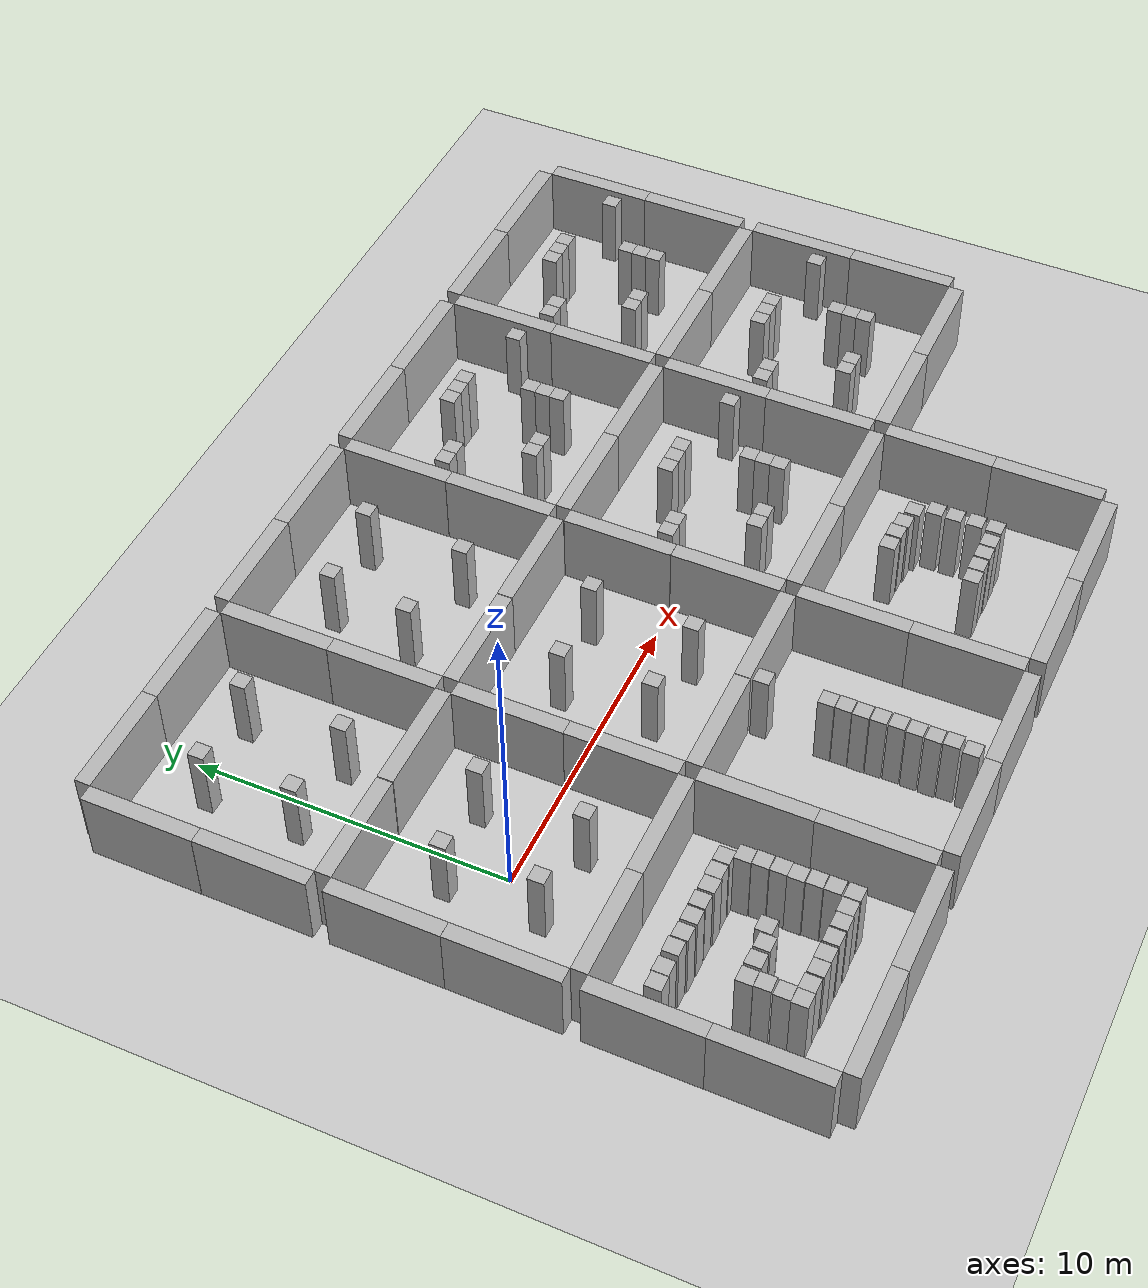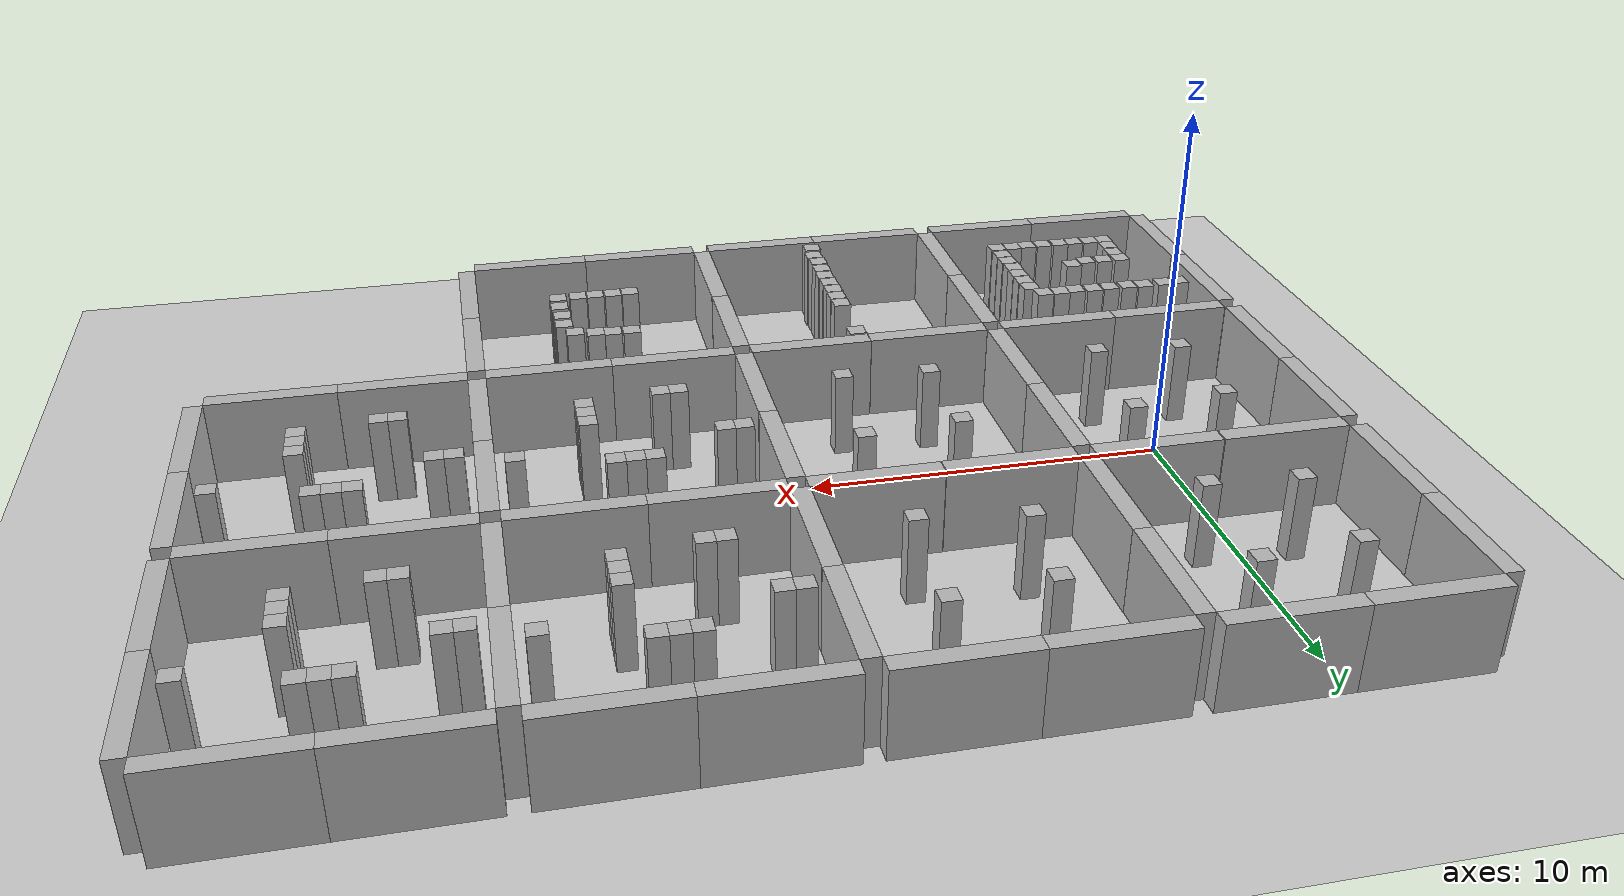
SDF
<sdf version="1.6">
 <world name="default">
  <light name="sun" type="directional">
   <pose>0 0 10 0 -0 0</pose>
   <diffuse>0.8 0.8 0.8 1</diffuse>
   <specular>0.1 0.1 0.1 1</specular>
   <attenuation>
    <range>1000</range>
    <constant>0.9</constant>
    <linear>0.01</linear>
    <quadratic>0.001</quadratic>
   </attenuation>
   <direction>-0.5 0.5 -1</direction>
  </light>
  <model name="ground_plane">
   <static>1</static>
   <link name="link">
    <collision name="collision">
     <geometry><plane><normal>0 0 1</normal><size>100 100</size></plane></geometry>
     <surface><friction><ode><mu>100</mu><mu2>50</mu2></ode></friction></surface>
    </collision>
    <visual name="visual">
     <cast_shadows>0</cast_shadows>
     <geometry><plane><normal>0 0 1</normal><size>100 100</size></plane></geometry>
     <material>
      <script><uri>file://media/materials/scripts/gazebo.material</uri><name>Gazebo/Grey</name></script>
     </material>
    </visual>
   </link>
  </model>
  <gravity>0 0 -9.8</gravity>
  <magnetic_field>6e-06 2.3e-05 -4.2e-05</magnetic_field>
  <atmosphere type="adiabatic"/>
  <physics name="default_physics" default="0" type="ode">
   <max_step_size>0.001</max_step_size>
   <real_time_factor>1</real_time_factor>
   <real_time_update_rate>1000</real_time_update_rate>
  </physics>
  <scene><ambient>0.4 0.4 0.4 1</ambient><background>0.7 0.7 0.7 1</background><shadows>1</shadows></scene>
  <spherical_coordinates>
   <surface_model>EARTH_WGS84</surface_model>
   <latitude_deg>0</latitude_deg>
   <longitude_deg>0</longitude_deg>
   <elevation>0</elevation>
   <heading_deg>0</heading_deg>
  </spherical_coordinates>
  <model name="mywall0_0">
   <static>1</static>
   <link name="link">
    <pose>0 0 1.4 0 -0 0</pose>
    <collision name="collision"><geometry><box><size>3.5 0.5 2.4</size></box></geometry></collision>
    <visual name="visual">
     <cast_shadows>0</cast_shadows>
     <geometry><box><size>3.5 0.5 2.4</size></box></geometry>
     <material>
      <script>
       <uri>model://mywall0/materials/scripts</uri>
       <uri>model://mywall0/materials/textures</uri>
       <name>vrc/mywall0</name>
      </script>
     </material>
    </visual>
   </link>
   <pose>1.77534 3.75 0 0 -0 0</pose>
  </model>
  <model name="mywall0_1">
   <static>1</static>
   <link name="link">
    <pose>0 0 1.4 0 -0 0</pose>
    <collision name="collision"><geometry><box><size>3.5 0.5 2.4</size></box></geometry></collision>
    <visual name="visual">
     <cast_shadows>0</cast_shadows>
     <geometry><box><size>3.5 0.5 2.4</size></box></geometry>
     <material>
      <script>
       <uri>model://mywall0/materials/scripts</uri>
       <uri>model://mywall0/materials/textures</uri>
       <name>vrc/mywall0</name>
      </script>
     </material>
    </visual>
   </link>
   <pose>-1.74865 3.75 0 0 -0 0</pose>
  </model>
  <model name="mywall0_2">
   <static>1</static>
   <link name="link">
    <pose>0 0 1.4 0 -0 0</pose>
    <collision name="collision"><geometry><box><size>3.5 0.5 2.4</size></box></geometry></collision>
    <visual name="visual">
     <cast_shadows>0</cast_shadows>
     <geometry><box><size>3.5 0.5 2.4</size></box></geometry>
     <material>
      <script>
       <uri>model://mywall0/materials/scripts</uri>
       <uri>model://mywall0/materials/textures</uri>
       <name>vrc/mywall0</name>
      </script>
     </material>
    </visual>
   </link>
   <pose>-1.73951 -3.75 0 0 -0 0</pose>
  </model>
  <model name="mywall0_3">
   <static>1</static>
   <link name="link">
    <pose>0 0 1.4 0 -0 0</pose>
    <collision name="collision"><geometry><box><size>3.5 0.5 2.4</size></box></geometry></collision>
    <visual name="visual">
     <cast_shadows>0</cast_shadows>
     <geometry><box><size>3.5 0.5 2.4</size></box></geometry>
     <material>
      <script>
       <uri>model://mywall0/materials/scripts</uri>
       <uri>model://mywall0/materials/textures</uri>
       <name>vrc/mywall0</name>
      </script>
     </material>
    </visual>
   </link>
   <pose>1.75778 -3.75 0 0 -0 0</pose>
  </model>
  <model name="mywall0_4">
   <static>1</static>
   <link name="link">
    <pose>0 0 1.4 0 -0 0</pose>
    <collision name="collision"><geometry><box><size>3.5 0.5 2.4</size></box></geometry></collision>
    <visual name="visual">
     <cast_shadows>0</cast_shadows>
     <geometry><box><size>3.5 0.5 2.4</size></box></geometry>
     <material>
      <script>
       <uri>model://mywall0/materials/scripts</uri>
       <uri>model://mywall0/materials/textures</uri>
       <name>vrc/mywall0</name>
      </script>
     </material>
    </visual>
   </link>
   <pose>-3.75 1.75 0 0 -0 1.57</pose>
  </model>
  <model name="mywall0_4_clone">
   <static>1</static>
   <link name="link">
    <pose>0 0 1.4 0 -0 0</pose>
    <collision name="collision"><geometry><box><size>3.5 0.5 2.4</size></box></geometry></collision>
    <visual name="visual">
     <cast_shadows>0</cast_shadows>
     <geometry><box><size>3.5 0.5 2.4</size></box></geometry>
     <material>
      <script>
       <uri>model://mywall0/materials/scripts</uri>
       <uri>model://mywall0/materials/textures</uri>
       <name>vrc/mywall0</name>
      </script>
     </material>
    </visual>
   </link>
   <pose>-3.7504 -1.75075 0 0 -0 1.57</pose>
  </model>
  <model name="mywall0_4_clone_0">
   <static>1</static>
   <link name="link">
    <pose>0 0 1.4 0 -0 0</pose>
    <collision name="collision"><geometry><box><size>3.5 0.5 2.4</size></box></geometry></collision>
    <visual name="visual">
     <cast_shadows>0</cast_shadows>
     <geometry><box><size>3.5 0.5 2.4</size></box></geometry>
     <material>
      <script>
       <uri>model://mywall0/materials/scripts</uri>
       <uri>model://mywall0/materials/textures</uri>
       <name>vrc/mywall0</name>
      </script>
     </material>
    </visual>
   </link>
   <pose>3.75 1.75 0 0 -0 1.57</pose>
  </model>
  <model name="mywall0_4_clone_1">
   <static>1</static>
   <link name="link">
    <pose>0 0 1.4 0 -0 0</pose>
    <collision name="collision"><geometry><box><size>3.5 0.5 2.4</size></box></geometry></collision>
    <visual name="visual">
     <cast_shadows>0</cast_shadows>
     <geometry><box><size>3.5 0.5 2.4</size></box></geometry>
     <material>
      <script>
       <uri>model://mywall0/materials/scripts</uri>
       <uri>model://mywall0/materials/textures</uri>
       <name>vrc/mywall0</name>
      </script>
     </material>
    </visual>
   </link>
   <pose>3.75 -1.75 0 0 -0 1.57</pose>
  </model>
  <model name="mywall0_4_clone_0_clone">
   <static>1</static>
   <link name="link">
    <pose>0 0 1.4 0 -0 0</pose>
    <collision name="collision"><geometry><box><size>3.5 0.5 2.4</size></box></geometry></collision>
    <visual name="visual">
     <cast_shadows>0</cast_shadows>
     <geometry><box><size>3.5 0.5 2.4</size></box></geometry>
     <material>
      <script>
       <uri>model://mywall0/materials/scripts</uri>
       <uri>model://mywall0/materials/textures</uri>
       <name>vrc/mywall0</name>
      </script>
     </material>
    </visual>
   </link>
   <pose>11.25 1.75 0 0 -0 1.57</pose>
  </model>
  <model name="mywall0_1_clone">
   <static>1</static>
   <link name="link">
    <pose>0 0 1.4 0 -0 0</pose>
    <collision name="collision"><geometry><box><size>3.5 0.5 2.4</size></box></geometry></collision>
    <visual name="visual">
     <cast_shadows>0</cast_shadows>
     <geometry><box><size>3.5 0.5 2.4</size></box></geometry>
     <material>
      <script>
       <uri>model://mywall0/materials/scripts</uri>
       <uri>model://mywall0/materials/textures</uri>
       <name>vrc/mywall0</name>
      </script>
     </material>
    </visual>
   </link>
   <pose>5.7511 3.75831 0 0 -0 0</pose>
  </model>
  <model name="mywall0_1_clone_0">
   <static>1</static>
   <link name="link">
    <pose>0 0 1.4 0 -0 0</pose>
    <collision name="collision"><geometry><box><size>3.5 0.5 2.4</size></box></geometry></collision>
    <visual name="visual">
     <cast_shadows>0</cast_shadows>
     <geometry><box><size>3.5 0.5 2.4</size></box></geometry>
     <material>
      <script>
       <uri>model://mywall0/materials/scripts</uri>
       <uri>model://mywall0/materials/textures</uri>
       <name>vrc/mywall0</name>
      </script>
     </material>
    </visual>
   </link>
   <pose>9.26518 3.76712 0 0 -0 0</pose>
  </model>
  <model name="mywall0_4_clone_0_clone_clone">
   <static>1</static>
   <link name="link">
    <pose>0 0 1.4 0 -0 0</pose>
    <collision name="collision"><geometry><box><size>3.5 0.5 2.4</size></box></geometry></collision>
    <visual name="visual">
     <cast_shadows>0</cast_shadows>
     <geometry><box><size>3.5 0.5 2.4</size></box></geometry>
     <material>
      <script>
       <uri>model://mywall0/materials/scripts</uri>
       <uri>model://mywall0/materials/textures</uri>
       <name>vrc/mywall0</name>
      </script>
     </material>
    </visual>
   </link>
   <pose>11.2541 -1.75467 0 0 -0 1.57</pose>
  </model>
  <model name="mywall0_3_clone">
   <static>1</static>
   <link name="link">
    <pose>0 0 1.4 0 -0 0</pose>
    <collision name="collision"><geometry><box><size>3.5 0.5 2.4</size></box></geometry></collision>
    <visual name="visual">
     <cast_shadows>0</cast_shadows>
     <geometry><box><size>3.5 0.5 2.4</size></box></geometry>
     <material>
      <script>
       <uri>model://mywall0/materials/scripts</uri>
       <uri>model://mywall0/materials/textures</uri>
       <name>vrc/mywall0</name>
      </script>
     </material>
    </visual>
   </link>
   <pose>5.75 -3.75829 0 0 -0 0</pose>
  </model>
  <model name="mywall0_3_clone_0">
   <static>1</static>
   <link name="link">
    <pose>0 0 1.4 0 -0 0</pose>
    <collision name="collision"><geometry><box><size>3.5 0.5 2.4</size></box></geometry></collision>
    <visual name="visual">
     <cast_shadows>0</cast_shadows>
     <geometry><box><size>3.5 0.5 2.4</size></box></geometry>
     <material>
      <script>
       <uri>model://mywall0/materials/scripts</uri>
       <uri>model://mywall0/materials/textures</uri>
       <name>vrc/mywall0</name>
      </script>
     </material>
    </visual>
   </link>
   <pose>9.25625 -3.75 0 0 -0 0</pose>
  </model>
  <model name="mywall0_1_clone_1">
   <static>1</static>
   <link name="link">
    <pose>0 0 1.4 0 -0 0</pose>
    <collision name="collision"><geometry><box><size>3.5 0.5 2.4</size></box></geometry></collision>
    <visual name="visual">
     <cast_shadows>0</cast_shadows>
     <geometry><box><size>3.5 0.5 2.4</size></box></geometry>
     <material>
      <script>
       <uri>model://mywall0/materials/scripts</uri>
       <uri>model://mywall0/materials/textures</uri>
       <name>vrc/mywall0</name>
      </script>
     </material>
    </visual>
   </link>
   <pose>13.25 3.75 0 0 -0 0</pose>
  </model>
  <model name="mywall0_1_clone_1_clone">
   <static>1</static>
   <link name="link">
    <pose>0 0 1.4 0 -0 0</pose>
    <collision name="collision"><geometry><box><size>3.5 0.5 2.4</size></box></geometry></collision>
    <visual name="visual">
     <cast_shadows>0</cast_shadows>
     <geometry><box><size>3.5 0.5 2.4</size></box></geometry>
     <material>
      <script>
       <uri>model://mywall0/materials/scripts</uri>
       <uri>model://mywall0/materials/textures</uri>
       <name>vrc/mywall0</name>
      </script>
     </material>
    </visual>
   </link>
   <pose>13.25 -3.75 0 0 -0 0</pose>
  </model>
  <model name="mywall0_1_clone_1_clone_0">
   <static>1</static>
   <link name="link">
    <pose>0 0 1.4 0 -0 0</pose>
    <collision name="collision"><geometry><box><size>3.5 0.5 2.4</size></box></geometry></collision>
    <visual name="visual">
     <cast_shadows>0</cast_shadows>
     <geometry><box><size>3.5 0.5 2.4</size></box></geometry>
     <material>
      <script>
       <uri>model://mywall0/materials/scripts</uri>
       <uri>model://mywall0/materials/textures</uri>
       <name>vrc/mywall0</name>
      </script>
     </material>
    </visual>
   </link>
   <pose>16.75 3.75 0 0 -0 0</pose>
  </model>
  <model name="mywall0_1_clone_1_clone_1">
   <static>1</static>
   <link name="link">
    <pose>0 0 1.4 0 -0 0</pose>
    <collision name="collision"><geometry><box><size>3.5 0.5 2.4</size></box></geometry></collision>
    <visual name="visual">
     <cast_shadows>0</cast_shadows>
     <geometry><box><size>3.5 0.5 2.4</size></box></geometry>
     <material>
      <script>
       <uri>model://mywall0/materials/scripts</uri>
       <uri>model://mywall0/materials/textures</uri>
       <name>vrc/mywall0</name>
      </script>
     </material>
    </visual>
   </link>
   <pose>16.75 -3.75 0 0 -0 0</pose>
  </model>
  <model name="mywall0_4_clone_0_clone_clone_0">
   <static>1</static>
   <link name="link">
    <pose>0 0 1.4 0 -0 0</pose>
    <collision name="collision"><geometry><box><size>3.5 0.5 2.4</size></box></geometry></collision>
    <visual name="visual">
     <cast_shadows>0</cast_shadows>
     <geometry><box><size>3.5 0.5 2.4</size></box></geometry>
     <material>
      <script>
       <uri>model://mywall0/materials/scripts</uri>
       <uri>model://mywall0/materials/textures</uri>
       <name>vrc/mywall0</name>
      </script>
     </material>
    </visual>
   </link>
   <pose>18.75 1.75 0 0 -0 1.57</pose>
  </model>
  <model name="mywall0_4_clone_0_clone_clone_0_clone">
   <static>1</static>
   <link name="link">
    <pose>0 0 1.4 0 -0 0</pose>
    <collision name="collision"><geometry><box><size>3.5 0.5 2.4</size></box></geometry></collision>
    <visual name="visual">
     <cast_shadows>0</cast_shadows>
     <geometry><box><size>3.5 0.5 2.4</size></box></geometry>
     <material>
      <script>
       <uri>model://mywall0/materials/scripts</uri>
       <uri>model://mywall0/materials/textures</uri>
       <name>vrc/mywall0</name>
      </script>
     </material>
    </visual>
   </link>
   <pose>18.75 -1.75 0 0 -0 1.57</pose>
  </model>
  <model name="mywall0_1_clone_1_clone_2">
   <static>1</static>
   <link name="link">
    <pose>0 0 1.4 0 -0 0</pose>
    <collision name="collision"><geometry><box><size>3.5 0.5 2.4</size></box></geometry></collision>
    <visual name="visual">
     <cast_shadows>0</cast_shadows>
     <geometry><box><size>3.5 0.5 2.4</size></box></geometry>
     <material>
      <script>
       <uri>model://mywall0/materials/scripts</uri>
       <uri>model://mywall0/materials/textures</uri>
       <name>vrc/mywall0</name>
      </script>
     </material>
    </visual>
   </link>
   <pose>20.75 3.75 0 0 -0 0</pose>
  </model>
  <model name="mywall0_1_clone_1_clone_3">
   <static>1</static>
   <link name="link">
    <pose>0 0 1.4 0 -0 0</pose>
    <collision name="collision"><geometry><box><size>3.5 0.5 2.4</size></box></geometry></collision>
    <visual name="visual">
     <cast_shadows>0</cast_shadows>
     <geometry><box><size>3.5 0.5 2.4</size></box></geometry>
     <material>
      <script>
       <uri>model://mywall0/materials/scripts</uri>
       <uri>model://mywall0/materials/textures</uri>
       <name>vrc/mywall0</name>
      </script>
     </material>
    </visual>
   </link>
   <pose>24.25 3.75 0 0 -0 0</pose>
  </model>
  <model name="mywall0_1_clone_1_clone_4">
   <static>1</static>
   <link name="link">
    <pose>0 0 1.4 0 -0 0</pose>
    <collision name="collision"><geometry><box><size>3.5 0.5 2.4</size></box></geometry></collision>
    <visual name="visual">
     <cast_shadows>0</cast_shadows>
     <geometry><box><size>3.5 0.5 2.4</size></box></geometry>
     <material>
      <script>
       <uri>model://mywall0/materials/scripts</uri>
       <uri>model://mywall0/materials/textures</uri>
       <name>vrc/mywall0</name>
      </script>
     </material>
    </visual>
   </link>
   <pose>20.75 -3.75 0 0 -0 0</pose>
  </model>
  <model name="mywall0_1_clone_1_clone_5">
   <static>1</static>
   <link name="link">
    <pose>0 0 1.4 0 -0 0</pose>
    <collision name="collision"><geometry><box><size>3.5 0.5 2.4</size></box></geometry></collision>
    <visual name="visual">
     <cast_shadows>0</cast_shadows>
     <geometry><box><size>3.5 0.5 2.4</size></box></geometry>
     <material>
      <script>
       <uri>model://mywall0/materials/scripts</uri>
       <uri>model://mywall0/materials/textures</uri>
       <name>vrc/mywall0</name>
      </script>
     </material>
    </visual>
   </link>
   <pose>24.25 -3.75 0 0 -0 0</pose>
  </model>
  <model name="mywall0_4_clone_0_clone_clone_0_clone_0">
   <static>1</static>
   <link name="link">
    <pose>0 0 1.4 0 -0 0</pose>
    <collision name="collision"><geometry><box><size>3.5 0.5 2.4</size></box></geometry></collision>
    <visual name="visual">
     <cast_shadows>0</cast_shadows>
     <geometry><box><size>3.5 0.5 2.4</size></box></geometry>
     <material>
      <script>
       <uri>model://mywall0/materials/scripts</uri>
       <uri>model://mywall0/materials/textures</uri>
       <name>vrc/mywall0</name>
      </script>
     </material>
    </visual>
   </link>
   <pose>26.25 1.75 0 0 -0 1.57</pose>
  </model>
  <model name="mywall0_4_clone_0_clone_clone_0_clone_1">
   <static>1</static>
   <link name="link">
    <pose>0 0 1.4 0 -0 0</pose>
    <collision name="collision"><geometry><box><size>3.5 0.5 2.4</size></box></geometry></collision>
    <visual name="visual">
     <cast_shadows>0</cast_shadows>
     <geometry><box><size>3.5 0.5 2.4</size></box></geometry>
     <material>
      <script>
       <uri>model://mywall0/materials/scripts</uri>
       <uri>model://mywall0/materials/textures</uri>
       <name>vrc/mywall0</name>
      </script>
     </material>
    </visual>
   </link>
   <pose>26.25 -1.75 0 0 -0 1.57</pose>
  </model>
  <model name="mywall0_4_clone_0_clone_clone_0_clone_2">
   <static>1</static>
   <link name="link">
    <pose>0 0 1.4 0 -0 0</pose>
    <collision name="collision"><geometry><box><size>3.5 0.5 2.4</size></box></geometry></collision>
    <visual name="visual">
     <cast_shadows>0</cast_shadows>
     <geometry><box><size>3.5 0.5 2.4</size></box></geometry>
     <material>
      <script>
       <uri>model://mywall0/materials/scripts</uri>
       <uri>model://mywall0/materials/textures</uri>
       <name>vrc/mywall0</name>
      </script>
     </material>
    </visual>
   </link>
   <pose>-3.75 5.75 0 0 -0 1.57</pose>
  </model>
  <model name="mywall0_4_clone_0_clone_clone_0_clone_3">
   <static>1</static>
   <link name="link">
    <pose>0 0 1.4 0 -0 0</pose>
    <collision name="collision"><geometry><box><size>3.5 0.5 2.4</size></box></geometry></collision>
    <visual name="visual">
     <cast_shadows>0</cast_shadows>
     <geometry><box><size>3.5 0.5 2.4</size></box></geometry>
     <material>
      <script>
       <uri>model://mywall0/materials/scripts</uri>
       <uri>model://mywall0/materials/textures</uri>
       <name>vrc/mywall0</name>
      </script>
     </material>
    </visual>
   </link>
   <pose>-3.75 9.25 0 0 -0 1.57</pose>
  </model>
  <model name="mywall0_4_clone_0_clone_clone_0_clone_4">
   <static>1</static>
   <link name="link">
    <pose>0 0 1.4 0 -0 0</pose>
    <collision name="collision"><geometry><box><size>3.5 0.5 2.4</size></box></geometry></collision>
    <visual name="visual">
     <cast_shadows>0</cast_shadows>
     <geometry><box><size>3.5 0.5 2.4</size></box></geometry>
     <material>
      <script>
       <uri>model://mywall0/materials/scripts</uri>
       <uri>model://mywall0/materials/textures</uri>
       <name>vrc/mywall0</name>
      </script>
     </material>
    </visual>
   </link>
   <pose>3.75 5.75 0 0 -0 1.57</pose>
  </model>
  <model name="mywall0_4_clone_0_clone_clone_0_clone_5">
   <static>1</static>
   <link name="link">
    <pose>0 0 1.4 0 -0 0</pose>
    <collision name="collision"><geometry><box><size>3.5 0.5 2.4</size></box></geometry></collision>
    <visual name="visual">
     <cast_shadows>0</cast_shadows>
     <geometry><box><size>3.5 0.5 2.4</size></box></geometry>
     <material>
      <script>
       <uri>model://mywall0/materials/scripts</uri>
       <uri>model://mywall0/materials/textures</uri>
       <name>vrc/mywall0</name>
      </script>
     </material>
    </visual>
   </link>
   <pose>3.75 9.25 0 0 -0 1.57</pose>
  </model>
  <model name="mywall0_4_clone_0_clone_clone_0_clone_6">
   <static>1</static>
   <link name="link">
    <pose>0 0 1.4 0 -0 0</pose>
    <collision name="collision"><geometry><box><size>3.5 0.5 2.4</size></box></geometry></collision>
    <visual name="visual">
     <cast_shadows>0</cast_shadows>
     <geometry><box><size>3.5 0.5 2.4</size></box></geometry>
     <material>
      <script>
       <uri>model://mywall0/materials/scripts</uri>
       <uri>model://mywall0/materials/textures</uri>
       <name>vrc/mywall0</name>
      </script>
     </material>
    </visual>
   </link>
   <pose>11.25 5.75 0 0 -0 1.57</pose>
  </model>
  <model name="mywall0_4_clone_0_clone_clone_0_clone_7">
   <static>1</static>
   <link name="link">
    <pose>0 0 1.4 0 -0 0</pose>
    <collision name="collision"><geometry><box><size>3.5 0.5 2.4</size></box></geometry></collision>
    <visual name="visual">
     <cast_shadows>0</cast_shadows>
     <geometry><box><size>3.5 0.5 2.4</size></box></geometry>
     <material>
      <script>
       <uri>model://mywall0/materials/scripts</uri>
       <uri>model://mywall0/materials/textures</uri>
       <name>vrc/mywall0</name>
      </script>
     </material>
    </visual>
   </link>
   <pose>11.25 9.25 0 0 -0 1.57</pose>
  </model>
  <model name="mywall0_4_clone_0_clone_clone_0_clone_8">
   <static>1</static>
   <link name="link">
    <pose>0 0 1.4 0 -0 0</pose>
    <collision name="collision"><geometry><box><size>3.5 0.5 2.4</size></box></geometry></collision>
    <visual name="visual">
     <cast_shadows>0</cast_shadows>
     <geometry><box><size>3.5 0.5 2.4</size></box></geometry>
     <material>
      <script>
       <uri>model://mywall0/materials/scripts</uri>
       <uri>model://mywall0/materials/textures</uri>
       <name>vrc/mywall0</name>
      </script>
     </material>
    </visual>
   </link>
   <pose>18.75 5.75 0 0 -0 1.57</pose>
  </model>
  <model name="mywall0_4_clone_0_clone_clone_0_clone_9">
   <static>1</static>
   <link name="link">
    <pose>0 0 1.4 0 -0 0</pose>
    <collision name="collision"><geometry><box><size>3.5 0.5 2.4</size></box></geometry></collision>
    <visual name="visual">
     <cast_shadows>0</cast_shadows>
     <geometry><box><size>3.5 0.5 2.4</size></box></geometry>
     <material>
      <script>
       <uri>model://mywall0/materials/scripts</uri>
       <uri>model://mywall0/materials/textures</uri>
       <name>vrc/mywall0</name>
      </script>
     </material>
    </visual>
   </link>
   <pose>18.75 9.25 0 0 -0 1.57</pose>
  </model>
  <model name="mywall0_4_clone_0_clone_clone_0_clone_10">
   <static>1</static>
   <link name="link">
    <pose>0 0 1.4 0 -0 0</pose>
    <collision name="collision"><geometry><box><size>3.5 0.5 2.4</size></box></geometry></collision>
    <visual name="visual">
     <cast_shadows>0</cast_shadows>
     <geometry><box><size>3.5 0.5 2.4</size></box></geometry>
     <material>
      <script>
       <uri>model://mywall0/materials/scripts</uri>
       <uri>model://mywall0/materials/textures</uri>
       <name>vrc/mywall0</name>
      </script>
     </material>
    </visual>
   </link>
   <pose>26.25 5.75 0 0 -0 1.57</pose>
  </model>
  <model name="mywall0_4_clone_0_clone_clone_0_clone_11">
   <static>1</static>
   <link name="link">
    <pose>0 0 1.4 0 -0 0</pose>
    <collision name="collision"><geometry><box><size>3.5 0.5 2.4</size></box></geometry></collision>
    <visual name="visual">
     <cast_shadows>0</cast_shadows>
     <geometry><box><size>3.5 0.5 2.4</size></box></geometry>
     <material>
      <script>
       <uri>model://mywall0/materials/scripts</uri>
       <uri>model://mywall0/materials/textures</uri>
       <name>vrc/mywall0</name>
      </script>
     </material>
    </visual>
   </link>
   <pose>26.25 9.25 0 0 -0 1.57</pose>
  </model>
  <model name="mywall0_1_clone_1_clone_3_clone">
   <static>1</static>
   <link name="link">
    <pose>0 0 1.4 0 -0 0</pose>
    <collision name="collision"><geometry><box><size>3.5 0.5 2.4</size></box></geometry></collision>
    <visual name="visual">
     <cast_shadows>0</cast_shadows>
     <geometry><box><size>3.5 0.5 2.4</size></box></geometry>
     <material>
      <script>
       <uri>model://mywall0/materials/scripts</uri>
       <uri>model://mywall0/materials/textures</uri>
       <name>vrc/mywall0</name>
      </script>
     </material>
    </visual>
   </link>
   <pose>24.25 11.25 0 0 -0 0</pose>
  </model>
  <model name="mywall0_1_clone_1_clone_3_clone_0">
   <static>1</static>
   <link name="link">
    <pose>0 0 1.4 0 -0 0</pose>
    <collision name="collision"><geometry><box><size>3.5 0.5 2.4</size></box></geometry></collision>
    <visual name="visual">
     <cast_shadows>0</cast_shadows>
     <geometry><box><size>3.5 0.5 2.4</size></box></geometry>
     <material>
      <script>
       <uri>model://mywall0/materials/scripts</uri>
       <uri>model://mywall0/materials/textures</uri>
       <name>vrc/mywall0</name>
      </script>
     </material>
    </visual>
   </link>
   <pose>20.75 11.25 0 0 -0 0</pose>
  </model>
  <model name="mywall0_1_clone_1_clone_3_clone_1">
   <static>1</static>
   <link name="link">
    <pose>0 0 1.4 0 -0 0</pose>
    <collision name="collision"><geometry><box><size>3.5 0.5 2.4</size></box></geometry></collision>
    <visual name="visual">
     <cast_shadows>0</cast_shadows>
     <geometry><box><size>3.5 0.5 2.4</size></box></geometry>
     <material>
      <script>
       <uri>model://mywall0/materials/scripts</uri>
       <uri>model://mywall0/materials/textures</uri>
       <name>vrc/mywall0</name>
      </script>
     </material>
    </visual>
   </link>
   <pose>16.75 11.25 0 0 -0 0</pose>
  </model>
  <model name="mywall0_1_clone_1_clone_3_clone_2">
   <static>1</static>
   <link name="link">
    <pose>0 0 1.4 0 -0 0</pose>
    <collision name="collision"><geometry><box><size>3.5 0.5 2.4</size></box></geometry></collision>
    <visual name="visual">
     <cast_shadows>0</cast_shadows>
     <geometry><box><size>3.5 0.5 2.4</size></box></geometry>
     <material>
      <script>
       <uri>model://mywall0/materials/scripts</uri>
       <uri>model://mywall0/materials/textures</uri>
       <name>vrc/mywall0</name>
      </script>
     </material>
    </visual>
   </link>
   <pose>13.25 11.25 0 0 -0 0</pose>
  </model>
  <model name="mywall0_1_clone_1_clone_3_clone_3">
   <static>1</static>
   <link name="link">
    <pose>0 0 1.4 0 -0 0</pose>
    <collision name="collision"><geometry><box><size>3.5 0.5 2.4</size></box></geometry></collision>
    <visual name="visual">
     <cast_shadows>0</cast_shadows>
     <geometry><box><size>3.5 0.5 2.4</size></box></geometry>
     <material>
      <script>
       <uri>model://mywall0/materials/scripts</uri>
       <uri>model://mywall0/materials/textures</uri>
       <name>vrc/mywall0</name>
      </script>
     </material>
    </visual>
   </link>
   <pose>9.25 11.25 0 0 -0 0</pose>
  </model>
  <model name="mywall0_1_clone_1_clone_3_clone_4">
   <static>1</static>
   <link name="link">
    <pose>0 0 1.4 0 -0 0</pose>
    <collision name="collision"><geometry><box><size>3.5 0.5 2.4</size></box></geometry></collision>
    <visual name="visual">
     <cast_shadows>0</cast_shadows>
     <geometry><box><size>3.5 0.5 2.4</size></box></geometry>
     <material>
      <script>
       <uri>model://mywall0/materials/scripts</uri>
       <uri>model://mywall0/materials/textures</uri>
       <name>vrc/mywall0</name>
      </script>
     </material>
    </visual>
   </link>
   <pose>5.75 11.25 0 0 -0 0</pose>
  </model>
  <model name="mywall0_1_clone_1_clone_3_clone_5">
   <static>1</static>
   <link name="link">
    <pose>0 0 1.4 0 -0 0</pose>
    <collision name="collision"><geometry><box><size>3.5 0.5 2.4</size></box></geometry></collision>
    <visual name="visual">
     <cast_shadows>0</cast_shadows>
     <geometry><box><size>3.5 0.5 2.4</size></box></geometry>
     <material>
      <script>
       <uri>model://mywall0/materials/scripts</uri>
       <uri>model://mywall0/materials/textures</uri>
       <name>vrc/mywall0</name>
      </script>
     </material>
    </visual>
   </link>
   <pose>-1.75 11.25 0 0 -0 0</pose>
  </model>
  <model name="mywall0_1_clone_1_clone_3_clone_6">
   <static>1</static>
   <link name="link">
    <pose>0 0 1.4 0 -0 0</pose>
    <collision name="collision"><geometry><box><size>3.5 0.5 2.4</size></box></geometry></collision>
    <visual name="visual">
     <cast_shadows>0</cast_shadows>
     <geometry><box><size>3.5 0.5 2.4</size></box></geometry>
     <material>
      <script>
       <uri>model://mywall0/materials/scripts</uri>
       <uri>model://mywall0/materials/textures</uri>
       <name>vrc/mywall0</name>
      </script>
     </material>
    </visual>
   </link>
   <pose>1.75 11.25 0 0 -0 0</pose>
  </model>
  <model name="mypillar">
   <static>1</static>
   <link name="link">
    <pose>0 0 1.4 0 -0 0</pose>
    <collision name="collision"><geometry><box><size>0.5 0.5 2.4</size></box></geometry></collision>
    <visual name="visual">
     <cast_shadows>0</cast_shadows>
     <geometry><box><size>0.5 0.5 2.4</size></box></geometry>
     <material>
      <script>
       <uri>model://mypillar/materials/scripts</uri>
       <uri>model://mypillar/materials/textures</uri>
       <name>vrc/mypillar</name>
      </script>
     </material>
    </visual>
   </link>
   <pose>6.3 1.4 0 0 -0 0</pose>
  </model>
  <model name="mypillar_0">
   <static>1</static>
   <link name="link">
    <pose>0 0 1.4 0 -0 0</pose>
    <collision name="collision"><geometry><box><size>0.5 0.5 2.4</size></box></geometry></collision>
    <visual name="visual">
     <cast_shadows>0</cast_shadows>
     <geometry><box><size>0.5 0.5 2.4</size></box></geometry>
     <material>
      <script>
       <uri>model://mypillar/materials/scripts</uri>
       <uri>model://mypillar/materials/textures</uri>
       <name>vrc/mypillar</name>
      </script>
     </material>
    </visual>
   </link>
   <pose>8.8 -1.7 0 0 -0 0</pose>
  </model>
  <model name="mypillar_1">
   <static>1</static>
   <link name="link">
    <pose>0 0 1.4 0 -0 0</pose>
    <collision name="collision"><geometry><box><size>0.5 0.5 2.4</size></box></geometry></collision>
    <visual name="visual">
     <cast_shadows>0</cast_shadows>
     <geometry><box><size>0.5 0.5 2.4</size></box></geometry>
     <material>
      <script>
       <uri>model://mypillar/materials/scripts</uri>
       <uri>model://mypillar/materials/textures</uri>
       <name>vrc/mypillar</name>
      </script>
     </material>
    </visual>
   </link>
   <pose>9 1.65 0 0 -0 0</pose>
  </model>
  <model name="mypillar_clone">
   <static>1</static>
   <link name="link">
    <pose>0 0 1.4 0 -0 0</pose>
    <collision name="collision"><geometry><box><size>0.5 0.5 2.4</size></box></geometry></collision>
    <visual name="visual">
     <cast_shadows>0</cast_shadows>
     <geometry><box><size>0.5 0.5 2.4</size></box></geometry>
     <material>
      <script>
       <uri>model://mypillar/materials/scripts</uri>
       <uri>model://mypillar/materials/textures</uri>
       <name>vrc/mypillar</name>
      </script>
     </material>
    </visual>
   </link>
   <pose>6.35 -1.5 0 0 -0 0</pose>
  </model>
  <model name="mypillar_clone_0">
   <static>1</static>
   <link name="link">
    <pose>0 0 1.4 0 -0 0</pose>
    <collision name="collision"><geometry><box><size>0.5 0.5 2.4</size></box></geometry></collision>
    <visual name="visual">
     <cast_shadows>0</cast_shadows>
     <geometry><box><size>0.5 0.5 2.4</size></box></geometry>
     <material>
      <script>
       <uri>model://mypillar/materials/scripts</uri>
       <uri>model://mypillar/materials/textures</uri>
       <name>vrc/mypillar</name>
      </script>
     </material>
    </visual>
   </link>
   <pose>-1.2 1.4 0 0 -0 0</pose>
  </model>
  <model name="mypillar_clone_clone">
   <static>1</static>
   <link name="link">
    <pose>0 0 1.4 0 -0 0</pose>
    <collision name="collision"><geometry><box><size>0.5 0.5 2.4</size></box></geometry></collision>
    <visual name="visual">
     <cast_shadows>0</cast_shadows>
     <geometry><box><size>0.5 0.5 2.4</size></box></geometry>
     <material>
      <script>
       <uri>model://mypillar/materials/scripts</uri>
       <uri>model://mypillar/materials/textures</uri>
       <name>vrc/mypillar</name>
      </script>
     </material>
    </visual>
   </link>
   <pose>-1.15 -1.5 0 0 -0 0</pose>
  </model>
  <model name="mypillar_0_clone">
   <static>1</static>
   <link name="link">
    <pose>0 0 1.4 0 -0 0</pose>
    <collision name="collision"><geometry><box><size>0.5 0.5 2.4</size></box></geometry></collision>
    <visual name="visual">
     <cast_shadows>0</cast_shadows>
     <geometry><box><size>0.5 0.5 2.4</size></box></geometry>
     <material>
      <script>
       <uri>model://mypillar/materials/scripts</uri>
       <uri>model://mypillar/materials/textures</uri>
       <name>vrc/mypillar</name>
      </script>
     </material>
    </visual>
   </link>
   <pose>1.3 -1.7 0 0 -0 0</pose>
  </model>
  <model name="mypillar_1_clone">
   <static>1</static>
   <link name="link">
    <pose>0 0 1.4 0 -0 0</pose>
    <collision name="collision"><geometry><box><size>0.5 0.5 2.4</size></box></geometry></collision>
    <visual name="visual">
     <cast_shadows>0</cast_shadows>
     <geometry><box><size>0.5 0.5 2.4</size></box></geometry>
     <material>
      <script>
       <uri>model://mypillar/materials/scripts</uri>
       <uri>model://mypillar/materials/textures</uri>
       <name>vrc/mypillar</name>
      </script>
     </material>
    </visual>
   </link>
   <pose>1.5 1.65 0 0 -0 0</pose>
  </model>
  <model name="mypillar_1_clone_clone">
   <static>1</static>
   <link name="link">
    <pose>0 0 1.4 0 -0 0</pose>
    <collision name="collision"><geometry><box><size>0.5 0.5 2.4</size></box></geometry></collision>
    <visual name="visual">
     <cast_shadows>0</cast_shadows>
     <geometry><box><size>0.5 0.5 2.4</size></box></geometry>
     <material>
      <script>
       <uri>model://mypillar/materials/scripts</uri>
       <uri>model://mypillar/materials/textures</uri>
       <name>vrc/mypillar</name>
      </script>
     </material>
    </visual>
   </link>
   <pose>15 1.6 0 0 -0 0</pose>
  </model>
  <model name="mypillar_1_clone_clone_0">
   <static>1</static>
   <link name="link">
    <pose>0 0 1.4 0 -0 0</pose>
    <collision name="collision"><geometry><box><size>0.5 0.5 2.4</size></box></geometry></collision>
    <visual name="visual">
     <cast_shadows>0</cast_shadows>
     <geometry><box><size>0.5 0.5 2.4</size></box></geometry>
     <material>
      <script>
       <uri>model://mypillar/materials/scripts</uri>
       <uri>model://mypillar/materials/textures</uri>
       <name>vrc/mypillar</name>
      </script>
     </material>
    </visual>
   </link>
   <pose>15.5 1.6 0 0 -0 0</pose>
  </model>
  <model name="mypillar_1_clone_clone_1">
   <static>1</static>
   <link name="link">
    <pose>0 0 1.4 0 -0 0</pose>
    <collision name="collision"><geometry><box><size>0.5 0.5 2.4</size></box></geometry></collision>
    <visual name="visual">
     <cast_shadows>0</cast_shadows>
     <geometry><box><size>0.5 0.5 2.4</size></box></geometry>
     <material>
      <script>
       <uri>model://mypillar/materials/scripts</uri>
       <uri>model://mypillar/materials/textures</uri>
       <name>vrc/mypillar</name>
      </script>
     </material>
    </visual>
   </link>
   <pose>14.5 1.6 0 0 -0 0</pose>
  </model>
  <model name="mypillar_1_clone_clone_2">
   <static>1</static>
   <link name="link">
    <pose>0 0 1.4 0 -0 0</pose>
    <collision name="collision"><geometry><box><size>0.5 0.5 2.4</size></box></geometry></collision>
    <visual name="visual">
     <cast_shadows>0</cast_shadows>
     <geometry><box><size>0.5 0.5 2.4</size></box></geometry>
     <material>
      <script>
       <uri>model://mypillar/materials/scripts</uri>
       <uri>model://mypillar/materials/textures</uri>
       <name>vrc/mypillar</name>
      </script>
     </material>
    </visual>
   </link>
   <pose>13.4 -1.8 0 0 -0 0</pose>
  </model>
  <model name="mypillar_1_clone_clone_3">
   <static>1</static>
   <link name="link">
    <pose>0 0 1.4 0 -0 0</pose>
    <collision name="collision"><geometry><box><size>0.5 0.5 2.4</size></box></geometry></collision>
    <visual name="visual">
     <cast_shadows>0</cast_shadows>
     <geometry><box><size>0.5 0.5 2.4</size></box></geometry>
     <material>
      <script>
       <uri>model://mypillar/materials/scripts</uri>
       <uri>model://mypillar/materials/textures</uri>
       <name>vrc/mypillar</name>
      </script>
     </material>
    </visual>
   </link>
   <pose>13.9 -1.8 0 0 -0 0</pose>
  </model>
  <model name="mypillar_1_clone_clone_4">
   <static>1</static>
   <link name="link">
    <pose>0 0 1.4 0 -0 0</pose>
    <collision name="collision"><geometry><box><size>0.5 0.5 2.4</size></box></geometry></collision>
    <visual name="visual">
     <cast_shadows>0</cast_shadows>
     <geometry><box><size>0.5 0.5 2.4</size></box></geometry>
     <material>
      <script>
       <uri>model://mypillar/materials/scripts</uri>
       <uri>model://mypillar/materials/textures</uri>
       <name>vrc/mypillar</name>
      </script>
     </material>
    </visual>
   </link>
   <pose>16 -1.5 0 0 -0 0</pose>
  </model>
  <model name="mypillar_1_clone_clone_4_clone">
   <static>1</static>
   <link name="link">
    <pose>0 0 1.4 0 -0 0</pose>
    <collision name="collision"><geometry><box><size>0.5 0.5 2.4</size></box></geometry></collision>
    <visual name="visual">
     <cast_shadows>0</cast_shadows>
     <geometry><box><size>0.5 0.5 2.4</size></box></geometry>
     <material>
      <script>
       <uri>model://mypillar/materials/scripts</uri>
       <uri>model://mypillar/materials/textures</uri>
       <name>vrc/mypillar</name>
      </script>
     </material>
    </visual>
   </link>
   <pose>16 -1 0 0 -0 0</pose>
  </model>
  <model name="mypillar_1_clone_clone_4_clone_0">
   <static>1</static>
   <link name="link">
    <pose>0 0 1.4 0 -0 0</pose>
    <collision name="collision"><geometry><box><size>0.5 0.5 2.4</size></box></geometry></collision>
    <visual name="visual">
     <cast_shadows>0</cast_shadows>
     <geometry><box><size>0.5 0.5 2.4</size></box></geometry>
     <material>
      <script>
       <uri>model://mypillar/materials/scripts</uri>
       <uri>model://mypillar/materials/textures</uri>
       <name>vrc/mypillar</name>
      </script>
     </material>
    </visual>
   </link>
   <pose>16 -0.5 0 0 -0 0</pose>
  </model>
  <model name="mypillar_1_clone_clone_4_clone_1">
   <static>1</static>
   <link name="link">
    <pose>0 0 1.4 0 -0 0</pose>
    <collision name="collision"><geometry><box><size>0.5 0.5 2.4</size></box></geometry></collision>
    <visual name="visual">
     <cast_shadows>0</cast_shadows>
     <geometry><box><size>0.5 0.5 2.4</size></box></geometry>
     <material>
      <script>
       <uri>model://mypillar/materials/scripts</uri>
       <uri>model://mypillar/materials/textures</uri>
       <name>vrc/mypillar</name>
      </script>
     </material>
    </visual>
   </link>
   <pose>18 1 0 0 -0 0</pose>
  </model>
  <model name="mypillar_1_clone_clone_4_clone_2">
   <static>1</static>
   <link name="link">
    <pose>0 0 1.4 0 -0 0</pose>
    <collision name="collision"><geometry><box><size>0.5 0.5 2.4</size></box></geometry></collision>
    <visual name="visual">
     <cast_shadows>0</cast_shadows>
     <geometry><box><size>0.5 0.5 2.4</size></box></geometry>
     <material>
      <script>
       <uri>model://mypillar/materials/scripts</uri>
       <uri>model://mypillar/materials/textures</uri>
       <name>vrc/mypillar</name>
      </script>
     </material>
    </visual>
   </link>
   <pose>12 0.5 0 0 -0 0</pose>
  </model>
  <model name="mypillar_1_clone_clone_4_clone_3">
   <static>1</static>
   <link name="link">
    <pose>0 0 1.4 0 -0 0</pose>
    <collision name="collision"><geometry><box><size>0.5 0.5 2.4</size></box></geometry></collision>
    <visual name="visual">
     <cast_shadows>0</cast_shadows>
     <geometry><box><size>0.5 0.5 2.4</size></box></geometry>
     <material>
      <script>
       <uri>model://mypillar/materials/scripts</uri>
       <uri>model://mypillar/materials/textures</uri>
       <name>vrc/mypillar</name>
      </script>
     </material>
    </visual>
   </link>
   <pose>12.5 0.5 0 0 -0 0</pose>
  </model>
  <model name="mypillar_clone_0_clone">
   <static>1</static>
   <link name="link">
    <pose>0 0 1.4 0 -0 0</pose>
    <collision name="collision"><geometry><box><size>0.5 0.5 2.4</size></box></geometry></collision>
    <visual name="visual">
     <cast_shadows>0</cast_shadows>
     <geometry><box><size>0.5 0.5 2.4</size></box></geometry>
     <material>
      <script>
       <uri>model://mypillar/materials/scripts</uri>
       <uri>model://mypillar/materials/textures</uri>
       <name>vrc/mypillar</name>
      </script>
     </material>
    </visual>
   </link>
   <pose>-1.2 8.9 0 0 -0 0</pose>
  </model>
  <model name="mypillar_clone_0_clone_0">
   <static>1</static>
   <link name="link">
    <pose>0 0 1.4 0 -0 0</pose>
    <collision name="collision"><geometry><box><size>0.5 0.5 2.4</size></box></geometry></collision>
    <visual name="visual">
     <cast_shadows>0</cast_shadows>
     <geometry><box><size>0.5 0.5 2.4</size></box></geometry>
     <material>
      <script>
       <uri>model://mypillar/materials/scripts</uri>
       <uri>model://mypillar/materials/textures</uri>
       <name>vrc/mypillar</name>
      </script>
     </material>
    </visual>
   </link>
   <pose>-1.15 6 0 0 -0 0</pose>
  </model>
  <model name="mypillar_clone_0_clone_1">
   <static>1</static>
   <link name="link">
    <pose>0 0 1.4 0 -0 0</pose>
    <collision name="collision"><geometry><box><size>0.5 0.5 2.4</size></box></geometry></collision>
    <visual name="visual">
     <cast_shadows>0</cast_shadows>
     <geometry><box><size>0.5 0.5 2.4</size></box></geometry>
     <material>
      <script>
       <uri>model://mypillar/materials/scripts</uri>
       <uri>model://mypillar/materials/textures</uri>
       <name>vrc/mypillar</name>
      </script>
     </material>
    </visual>
   </link>
   <pose>1.5 9.15 0 0 -0 0</pose>
  </model>
  <model name="mypillar_clone_0_clone_2">
   <static>1</static>
   <link name="link">
    <pose>0 0 1.4 0 -0 0</pose>
    <collision name="collision"><geometry><box><size>0.5 0.5 2.4</size></box></geometry></collision>
    <visual name="visual">
     <cast_shadows>0</cast_shadows>
     <geometry><box><size>0.5 0.5 2.4</size></box></geometry>
     <material>
      <script>
       <uri>model://mypillar/materials/scripts</uri>
       <uri>model://mypillar/materials/textures</uri>
       <name>vrc/mypillar</name>
      </script>
     </material>
    </visual>
   </link>
   <pose>1.3 5.8 0 0 -0 0</pose>
  </model>
  <model name="mypillar_clone_0_clone_1_clone">
   <static>1</static>
   <link name="link">
    <pose>0 0 1.4 0 -0 0</pose>
    <collision name="collision"><geometry><box><size>0.5 0.5 2.4</size></box></geometry></collision>
    <visual name="visual">
     <cast_shadows>0</cast_shadows>
     <geometry><box><size>0.5 0.5 2.4</size></box></geometry>
     <material>
      <script>
       <uri>model://mypillar/materials/scripts</uri>
       <uri>model://mypillar/materials/textures</uri>
       <name>vrc/mypillar</name>
      </script>
     </material>
    </visual>
   </link>
   <pose>6.3 8.9 0 0 -0 0</pose>
  </model>
  <model name="mypillar_clone_0_clone_1_clone_0">
   <static>1</static>
   <link name="link">
    <pose>0 0 1.4 0 -0 0</pose>
    <collision name="collision"><geometry><box><size>0.5 0.5 2.4</size></box></geometry></collision>
    <visual name="visual">
     <cast_shadows>0</cast_shadows>
     <geometry><box><size>0.5 0.5 2.4</size></box></geometry>
     <material>
      <script>
       <uri>model://mypillar/materials/scripts</uri>
       <uri>model://mypillar/materials/textures</uri>
       <name>vrc/mypillar</name>
      </script>
     </material>
    </visual>
   </link>
   <pose>6.00869 6.21238 0 0 -0 0</pose>
  </model>
  <model name="mypillar_clone_0_clone_1_clone_1">
   <static>1</static>
   <link name="link">
    <pose>0 0 1.4 0 -0 0</pose>
    <collision name="collision"><geometry><box><size>0.5 0.5 2.4</size></box></geometry></collision>
    <visual name="visual">
     <cast_shadows>0</cast_shadows>
     <geometry><box><size>0.5 0.5 2.4</size></box></geometry>
     <material>
      <script>
       <uri>model://mypillar/materials/scripts</uri>
       <uri>model://mypillar/materials/textures</uri>
       <name>vrc/mypillar</name>
      </script>
     </material>
    </visual>
   </link>
   <pose>9 9.15 0 0 -0 0</pose>
  </model>
  <model name="mypillar_clone_0_clone_1_clone_2">
   <static>1</static>
   <link name="link">
    <pose>0 0 1.4 0 -0 0</pose>
    <collision name="collision"><geometry><box><size>0.5 0.5 2.4</size></box></geometry></collision>
    <visual name="visual">
     <cast_shadows>0</cast_shadows>
     <geometry><box><size>0.5 0.5 2.4</size></box></geometry>
     <material>
      <script>
       <uri>model://mypillar/materials/scripts</uri>
       <uri>model://mypillar/materials/textures</uri>
       <name>vrc/mypillar</name>
      </script>
     </material>
    </visual>
   </link>
   <pose>8.8 5.8 0 0 -0 0</pose>
  </model>
  <model name="mypillar_1_clone_clone_4_clone_2_clone">
   <static>1</static>
   <link name="link">
    <pose>0 0 1.4 0 -0 0</pose>
    <collision name="collision"><geometry><box><size>0.5 0.5 2.4</size></box></geometry></collision>
    <visual name="visual">
     <cast_shadows>0</cast_shadows>
     <geometry><box><size>0.5 0.5 2.4</size></box></geometry>
     <material>
      <script>
       <uri>model://mypillar/materials/scripts</uri>
       <uri>model://mypillar/materials/textures</uri>
       <name>vrc/mypillar</name>
      </script>
     </material>
    </visual>
   </link>
   <pose>12 8 0 0 -0 0</pose>
  </model>
  <model name="mypillar_1_clone_clone_4_clone_2_clone_0">
   <static>1</static>
   <link name="link">
    <pose>0 0 1.4 0 -0 0</pose>
    <collision name="collision"><geometry><box><size>0.5 0.5 2.4</size></box></geometry></collision>
    <visual name="visual">
     <cast_shadows>0</cast_shadows>
     <geometry><box><size>0.5 0.5 2.4</size></box></geometry>
     <material>
      <script>
       <uri>model://mypillar/materials/scripts</uri>
       <uri>model://mypillar/materials/textures</uri>
       <name>vrc/mypillar</name>
      </script>
     </material>
    </visual>
   </link>
   <pose>12.5 8 0 0 -0 0</pose>
  </model>
  <model name="mypillar_1_clone_clone_4_clone_2_clone_1">
   <static>1</static>
   <link name="link">
    <pose>0 0 1.4 0 -0 0</pose>
    <collision name="collision"><geometry><box><size>0.5 0.5 2.4</size></box></geometry></collision>
    <visual name="visual">
     <cast_shadows>0</cast_shadows>
     <geometry><box><size>0.5 0.5 2.4</size></box></geometry>
     <material>
      <script>
       <uri>model://mypillar/materials/scripts</uri>
       <uri>model://mypillar/materials/textures</uri>
       <name>vrc/mypillar</name>
      </script>
     </material>
    </visual>
   </link>
   <pose>14.5 9.1 0 0 -0 0</pose>
  </model>
  <model name="mypillar_1_clone_clone_4_clone_2_clone_2">
   <static>1</static>
   <link name="link">
    <pose>0 0 1.4 0 -0 0</pose>
    <collision name="collision"><geometry><box><size>0.5 0.5 2.4</size></box></geometry></collision>
    <visual name="visual">
     <cast_shadows>0</cast_shadows>
     <geometry><box><size>0.5 0.5 2.4</size></box></geometry>
     <material>
      <script>
       <uri>model://mypillar/materials/scripts</uri>
       <uri>model://mypillar/materials/textures</uri>
       <name>vrc/mypillar</name>
      </script>
     </material>
    </visual>
   </link>
   <pose>15 9.1 0 0 -0 0</pose>
  </model>
  <model name="mypillar_1_clone_clone_4_clone_2_clone_3">
   <static>1</static>
   <link name="link">
    <pose>0 0 1.4 0 -0 0</pose>
    <collision name="collision"><geometry><box><size>0.5 0.5 2.4</size></box></geometry></collision>
    <visual name="visual">
     <cast_shadows>0</cast_shadows>
     <geometry><box><size>0.5 0.5 2.4</size></box></geometry>
     <material>
      <script>
       <uri>model://mypillar/materials/scripts</uri>
       <uri>model://mypillar/materials/textures</uri>
       <name>vrc/mypillar</name>
      </script>
     </material>
    </visual>
   </link>
   <pose>15.5 9.1 0 0 -0 0</pose>
  </model>
  <model name="mypillar_1_clone_clone_4_clone_2_clone_4">
   <static>1</static>
   <link name="link">
    <pose>0 0 1.4 0 -0 0</pose>
    <collision name="collision"><geometry><box><size>0.5 0.5 2.4</size></box></geometry></collision>
    <visual name="visual">
     <cast_shadows>0</cast_shadows>
     <geometry><box><size>0.5 0.5 2.4</size></box></geometry>
     <material>
      <script>
       <uri>model://mypillar/materials/scripts</uri>
       <uri>model://mypillar/materials/textures</uri>
       <name>vrc/mypillar</name>
      </script>
     </material>
    </visual>
   </link>
   <pose>13.4 5.7 0 0 -0 0</pose>
  </model>
  <model name="mypillar_1_clone_clone_4_clone_2_clone_5">
   <static>1</static>
   <link name="link">
    <pose>0 0 1.4 0 -0 0</pose>
    <collision name="collision"><geometry><box><size>0.5 0.5 2.4</size></box></geometry></collision>
    <visual name="visual">
     <cast_shadows>0</cast_shadows>
     <geometry><box><size>0.5 0.5 2.4</size></box></geometry>
     <material>
      <script>
       <uri>model://mypillar/materials/scripts</uri>
       <uri>model://mypillar/materials/textures</uri>
       <name>vrc/mypillar</name>
      </script>
     </material>
    </visual>
   </link>
   <pose>13.9 5.7 0 0 -0 0</pose>
  </model>
  <model name="mypillar_1_clone_clone_4_clone_2_clone_6">
   <static>1</static>
   <link name="link">
    <pose>0 0 1.4 0 -0 0</pose>
    <collision name="collision"><geometry><box><size>0.5 0.5 2.4</size></box></geometry></collision>
    <visual name="visual">
     <cast_shadows>0</cast_shadows>
     <geometry><box><size>0.5 0.5 2.4</size></box></geometry>
     <material>
      <script>
       <uri>model://mypillar/materials/scripts</uri>
       <uri>model://mypillar/materials/textures</uri>
       <name>vrc/mypillar</name>
      </script>
     </material>
    </visual>
   </link>
   <pose>16 6.5 0 0 -0 0</pose>
  </model>
  <model name="mypillar_1_clone_clone_4_clone_2_clone_7">
   <static>1</static>
   <link name="link">
    <pose>0 0 1.4 0 -0 0</pose>
    <collision name="collision"><geometry><box><size>0.5 0.5 2.4</size></box></geometry></collision>
    <visual name="visual">
     <cast_shadows>0</cast_shadows>
     <geometry><box><size>0.5 0.5 2.4</size></box></geometry>
     <material>
      <script>
       <uri>model://mypillar/materials/scripts</uri>
       <uri>model://mypillar/materials/textures</uri>
       <name>vrc/mypillar</name>
      </script>
     </material>
    </visual>
   </link>
   <pose>16 6 0 0 -0 0</pose>
  </model>
  <model name="mypillar_1_clone_clone_4_clone_2_clone_8">
   <static>1</static>
   <link name="link">
    <pose>0 0 1.4 0 -0 0</pose>
    <collision name="collision"><geometry><box><size>0.5 0.5 2.4</size></box></geometry></collision>
    <visual name="visual">
     <cast_shadows>0</cast_shadows>
     <geometry><box><size>0.5 0.5 2.4</size></box></geometry>
     <material>
      <script>
       <uri>model://mypillar/materials/scripts</uri>
       <uri>model://mypillar/materials/textures</uri>
       <name>vrc/mypillar</name>
      </script>
     </material>
    </visual>
   </link>
   <pose>16 7 0 0 -0 0</pose>
  </model>
  <model name="mypillar_1_clone_clone_4_clone_2_clone_9">
   <static>1</static>
   <link name="link">
    <pose>0 0 1.4 0 -0 0</pose>
    <collision name="collision"><geometry><box><size>0.5 0.5 2.4</size></box></geometry></collision>
    <visual name="visual">
     <cast_shadows>0</cast_shadows>
     <geometry><box><size>0.5 0.5 2.4</size></box></geometry>
     <material>
      <script>
       <uri>model://mypillar/materials/scripts</uri>
       <uri>model://mypillar/materials/textures</uri>
       <name>vrc/mypillar</name>
      </script>
     </material>
    </visual>
   </link>
   <pose>18 8.5 0 0 -0 0</pose>
  </model>
  <model name="mypillar_1_clone_clone_4_clone_2_clone_10">
   <static>1</static>
   <link name="link">
    <pose>0 0 1.4 0 -0 0</pose>
    <collision name="collision"><geometry><box><size>0.5 0.5 2.4</size></box></geometry></collision>
    <visual name="visual">
     <cast_shadows>0</cast_shadows>
     <geometry><box><size>0.5 0.5 2.4</size></box></geometry>
     <material>
      <script>
       <uri>model://mypillar/materials/scripts</uri>
       <uri>model://mypillar/materials/textures</uri>
       <name>vrc/mypillar</name>
      </script>
     </material>
    </visual>
   </link>
   <pose>19.5 8 0 0 -0 0</pose>
  </model>
  <model name="mypillar_1_clone_clone_4_clone_2_clone_11">
   <static>1</static>
   <link name="link">
    <pose>0 0 1.4 0 -0 0</pose>
    <collision name="collision"><geometry><box><size>0.5 0.5 2.4</size></box></geometry></collision>
    <visual name="visual">
     <cast_shadows>0</cast_shadows>
     <geometry><box><size>0.5 0.5 2.4</size></box></geometry>
     <material>
      <script>
       <uri>model://mypillar/materials/scripts</uri>
       <uri>model://mypillar/materials/textures</uri>
       <name>vrc/mypillar</name>
      </script>
     </material>
    </visual>
   </link>
   <pose>20 8 0 0 -0 0</pose>
  </model>
  <model name="mypillar_1_clone_clone_4_clone_2_clone_12">
   <static>1</static>
   <link name="link">
    <pose>0 0 1.4 0 -0 0</pose>
    <collision name="collision"><geometry><box><size>0.5 0.5 2.4</size></box></geometry></collision>
    <visual name="visual">
     <cast_shadows>0</cast_shadows>
     <geometry><box><size>0.5 0.5 2.4</size></box></geometry>
     <material>
      <script>
       <uri>model://mypillar/materials/scripts</uri>
       <uri>model://mypillar/materials/textures</uri>
       <name>vrc/mypillar</name>
      </script>
     </material>
    </visual>
   </link>
   <pose>22 9.1 0 0 -0 0</pose>
  </model>
  <model name="mypillar_1_clone_clone_4_clone_2_clone_13">
   <static>1</static>
   <link name="link">
    <pose>0 0 1.4 0 -0 0</pose>
    <collision name="collision"><geometry><box><size>0.5 0.5 2.4</size></box></geometry></collision>
    <visual name="visual">
     <cast_shadows>0</cast_shadows>
     <geometry><box><size>0.5 0.5 2.4</size></box></geometry>
     <material>
      <script>
       <uri>model://mypillar/materials/scripts</uri>
       <uri>model://mypillar/materials/textures</uri>
       <name>vrc/mypillar</name>
      </script>
     </material>
    </visual>
   </link>
   <pose>22.5 9.1 0 0 -0 0</pose>
  </model>
  <model name="mypillar_1_clone_clone_4_clone_2_clone_14">
   <static>1</static>
   <link name="link">
    <pose>0 0 1.4 0 -0 0</pose>
    <collision name="collision"><geometry><box><size>0.5 0.5 2.4</size></box></geometry></collision>
    <visual name="visual">
     <cast_shadows>0</cast_shadows>
     <geometry><box><size>0.5 0.5 2.4</size></box></geometry>
     <material>
      <script>
       <uri>model://mypillar/materials/scripts</uri>
       <uri>model://mypillar/materials/textures</uri>
       <name>vrc/mypillar</name>
      </script>
     </material>
    </visual>
   </link>
   <pose>23 9.1 0 0 -0 0</pose>
  </model>
  <model name="mypillar_1_clone_clone_4_clone_2_clone_15">
   <static>1</static>
   <link name="link">
    <pose>0 0 1.4 0 -0 0</pose>
    <collision name="collision"><geometry><box><size>0.5 0.5 2.4</size></box></geometry></collision>
    <visual name="visual">
     <cast_shadows>0</cast_shadows>
     <geometry><box><size>0.5 0.5 2.4</size></box></geometry>
     <material>
      <script>
       <uri>model://mypillar/materials/scripts</uri>
       <uri>model://mypillar/materials/textures</uri>
       <name>vrc/mypillar</name>
      </script>
     </material>
    </visual>
   </link>
   <pose>25.5 8.5 0 0 -0 0</pose>
  </model>
  <model name="mypillar_1_clone_clone_4_clone_2_clone_16">
   <static>1</static>
   <link name="link">
    <pose>0 0 1.4 0 -0 0</pose>
    <collision name="collision"><geometry><box><size>0.5 0.5 2.4</size></box></geometry></collision>
    <visual name="visual">
     <cast_shadows>0</cast_shadows>
     <geometry><box><size>0.5 0.5 2.4</size></box></geometry>
     <material>
      <script>
       <uri>model://mypillar/materials/scripts</uri>
       <uri>model://mypillar/materials/textures</uri>
       <name>vrc/mypillar</name>
      </script>
     </material>
    </visual>
   </link>
   <pose>23.5 7 0 0 -0 0</pose>
  </model>
  <model name="mypillar_1_clone_clone_4_clone_2_clone_17">
   <static>1</static>
   <link name="link">
    <pose>0 0 1.4 0 -0 0</pose>
    <collision name="collision"><geometry><box><size>0.5 0.5 2.4</size></box></geometry></collision>
    <visual name="visual">
     <cast_shadows>0</cast_shadows>
     <geometry><box><size>0.5 0.5 2.4</size></box></geometry>
     <material>
      <script>
       <uri>model://mypillar/materials/scripts</uri>
       <uri>model://mypillar/materials/textures</uri>
       <name>vrc/mypillar</name>
      </script>
     </material>
    </visual>
   </link>
   <pose>23.5 6.5 0 0 -0 0</pose>
  </model>
  <model name="mypillar_1_clone_clone_4_clone_2_clone_18">
   <static>1</static>
   <link name="link">
    <pose>0 0 1.4 0 -0 0</pose>
    <collision name="collision"><geometry><box><size>0.5 0.5 2.4</size></box></geometry></collision>
    <visual name="visual">
     <cast_shadows>0</cast_shadows>
     <geometry><box><size>0.5 0.5 2.4</size></box></geometry>
     <material>
      <script>
       <uri>model://mypillar/materials/scripts</uri>
       <uri>model://mypillar/materials/textures</uri>
       <name>vrc/mypillar</name>
      </script>
     </material>
    </visual>
   </link>
   <pose>23.5 6 0 0 -0 0</pose>
  </model>
  <model name="mypillar_1_clone_clone_4_clone_2_clone_19">
   <static>1</static>
   <link name="link">
    <pose>0 0 1.4 0 -0 0</pose>
    <collision name="collision"><geometry><box><size>0.5 0.5 2.4</size></box></geometry></collision>
    <visual name="visual">
     <cast_shadows>0</cast_shadows>
     <geometry><box><size>0.5 0.5 2.4</size></box></geometry>
     <material>
      <script>
       <uri>model://mypillar/materials/scripts</uri>
       <uri>model://mypillar/materials/textures</uri>
       <name>vrc/mypillar</name>
      </script>
     </material>
    </visual>
   </link>
   <pose>20.9 5.7 0 0 -0 0</pose>
  </model>
  <model name="mypillar_1_clone_clone_4_clone_2_clone_20">
   <static>1</static>
   <link name="link">
    <pose>0 0 1.4 0 -0 0</pose>
    <collision name="collision"><geometry><box><size>0.5 0.5 2.4</size></box></geometry></collision>
    <visual name="visual">
     <cast_shadows>0</cast_shadows>
     <geometry><box><size>0.5 0.5 2.4</size></box></geometry>
     <material>
      <script>
       <uri>model://mypillar/materials/scripts</uri>
       <uri>model://mypillar/materials/textures</uri>
       <name>vrc/mypillar</name>
      </script>
     </material>
    </visual>
   </link>
   <pose>21.4 5.7 0 0 -0 0</pose>
  </model>
  <model name="mypillar_1_clone_clone_4_clone_2_clone_21">
   <static>1</static>
   <link name="link">
    <pose>0 0 1.4 0 -0 0</pose>
    <collision name="collision"><geometry><box><size>0.5 0.5 2.4</size></box></geometry></collision>
    <visual name="visual">
     <cast_shadows>0</cast_shadows>
     <geometry><box><size>0.5 0.5 2.4</size></box></geometry>
     <material>
      <script>
       <uri>model://mypillar/materials/scripts</uri>
       <uri>model://mypillar/materials/textures</uri>
       <name>vrc/mypillar</name>
      </script>
     </material>
    </visual>
   </link>
   <pose>19.5 0.5 0 0 -0 0</pose>
  </model>
  <model name="mypillar_1_clone_clone_4_clone_2_clone_22">
   <static>1</static>
   <link name="link">
    <pose>0 0 1.4 0 -0 0</pose>
    <collision name="collision"><geometry><box><size>0.5 0.5 2.4</size></box></geometry></collision>
    <visual name="visual">
     <cast_shadows>0</cast_shadows>
     <geometry><box><size>0.5 0.5 2.4</size></box></geometry>
     <material>
      <script>
       <uri>model://mypillar/materials/scripts</uri>
       <uri>model://mypillar/materials/textures</uri>
       <name>vrc/mypillar</name>
      </script>
     </material>
    </visual>
   </link>
   <pose>20 0.5 0 0 -0 0</pose>
  </model>
  <model name="mypillar_1_clone_clone_4_clone_2_clone_23">
   <static>1</static>
   <link name="link">
    <pose>0 0 1.4 0 -0 0</pose>
    <collision name="collision"><geometry><box><size>0.5 0.5 2.4</size></box></geometry></collision>
    <visual name="visual">
     <cast_shadows>0</cast_shadows>
     <geometry><box><size>0.5 0.5 2.4</size></box></geometry>
     <material>
      <script>
       <uri>model://mypillar/materials/scripts</uri>
       <uri>model://mypillar/materials/textures</uri>
       <name>vrc/mypillar</name>
      </script>
     </material>
    </visual>
   </link>
   <pose>22 1.6 0 0 -0 0</pose>
  </model>
  <model name="mypillar_1_clone_clone_4_clone_2_clone_24">
   <static>1</static>
   <link name="link">
    <pose>0 0 1.4 0 -0 0</pose>
    <collision name="collision"><geometry><box><size>0.5 0.5 2.4</size></box></geometry></collision>
    <visual name="visual">
     <cast_shadows>0</cast_shadows>
     <geometry><box><size>0.5 0.5 2.4</size></box></geometry>
     <material>
      <script>
       <uri>model://mypillar/materials/scripts</uri>
       <uri>model://mypillar/materials/textures</uri>
       <name>vrc/mypillar</name>
      </script>
     </material>
    </visual>
   </link>
   <pose>22.5 1.6 0 0 -0 0</pose>
  </model>
  <model name="mypillar_1_clone_clone_4_clone_2_clone_25">
   <static>1</static>
   <link name="link">
    <pose>0 0 1.4 0 -0 0</pose>
    <collision name="collision"><geometry><box><size>0.5 0.5 2.4</size></box></geometry></collision>
    <visual name="visual">
     <cast_shadows>0</cast_shadows>
     <geometry><box><size>0.5 0.5 2.4</size></box></geometry>
     <material>
      <script>
       <uri>model://mypillar/materials/scripts</uri>
       <uri>model://mypillar/materials/textures</uri>
       <name>vrc/mypillar</name>
      </script>
     </material>
    </visual>
   </link>
   <pose>23 1.6 0 0 -0 0</pose>
  </model>
  <model name="mypillar_1_clone_clone_4_clone_2_clone_26">
   <static>1</static>
   <link name="link">
    <pose>0 0 1.4 0 -0 0</pose>
    <collision name="collision"><geometry><box><size>0.5 0.5 2.4</size></box></geometry></collision>
    <visual name="visual">
     <cast_shadows>0</cast_shadows>
     <geometry><box><size>0.5 0.5 2.4</size></box></geometry>
     <material>
      <script>
       <uri>model://mypillar/materials/scripts</uri>
       <uri>model://mypillar/materials/textures</uri>
       <name>vrc/mypillar</name>
      </script>
     </material>
    </visual>
   </link>
   <pose>25.5 1 0 0 -0 0</pose>
  </model>
  <model name="mypillar_1_clone_clone_4_clone_2_clone_27">
   <static>1</static>
   <link name="link">
    <pose>0 0 1.4 0 -0 0</pose>
    <collision name="collision"><geometry><box><size>0.5 0.5 2.4</size></box></geometry></collision>
    <visual name="visual">
     <cast_shadows>0</cast_shadows>
     <geometry><box><size>0.5 0.5 2.4</size></box></geometry>
     <material>
      <script>
       <uri>model://mypillar/materials/scripts</uri>
       <uri>model://mypillar/materials/textures</uri>
       <name>vrc/mypillar</name>
      </script>
     </material>
    </visual>
   </link>
   <pose>23.5 -1 0 0 -0 0</pose>
  </model>
  <model name="mypillar_1_clone_clone_4_clone_2_clone_28">
   <static>1</static>
   <link name="link">
    <pose>0 0 1.4 0 -0 0</pose>
    <collision name="collision"><geometry><box><size>0.5 0.5 2.4</size></box></geometry></collision>
    <visual name="visual">
     <cast_shadows>0</cast_shadows>
     <geometry><box><size>0.5 0.5 2.4</size></box></geometry>
     <material>
      <script>
       <uri>model://mypillar/materials/scripts</uri>
       <uri>model://mypillar/materials/textures</uri>
       <name>vrc/mypillar</name>
      </script>
     </material>
    </visual>
   </link>
   <pose>23.5 -1.5 0 0 -0 0</pose>
  </model>
  <model name="mypillar_1_clone_clone_4_clone_2_clone_29">
   <static>1</static>
   <link name="link">
    <pose>0 0 1.4 0 -0 0</pose>
    <collision name="collision"><geometry><box><size>0.5 0.5 2.4</size></box></geometry></collision>
    <visual name="visual">
     <cast_shadows>0</cast_shadows>
     <geometry><box><size>0.5 0.5 2.4</size></box></geometry>
     <material>
      <script>
       <uri>model://mypillar/materials/scripts</uri>
       <uri>model://mypillar/materials/textures</uri>
       <name>vrc/mypillar</name>
      </script>
     </material>
    </visual>
   </link>
   <pose>23.5 -0.5 0 0 -0 0</pose>
  </model>
  <model name="mypillar_1_clone_clone_4_clone_2_clone_30">
   <static>1</static>
   <link name="link">
    <pose>0 0 1.4 0 -0 0</pose>
    <collision name="collision"><geometry><box><size>0.5 0.5 2.4</size></box></geometry></collision>
    <visual name="visual">
     <cast_shadows>0</cast_shadows>
     <geometry><box><size>0.5 0.5 2.4</size></box></geometry>
     <material>
      <script>
       <uri>model://mypillar/materials/scripts</uri>
       <uri>model://mypillar/materials/textures</uri>
       <name>vrc/mypillar</name>
      </script>
     </material>
    </visual>
   </link>
   <pose>20.9 -1.8 0 0 -0 0</pose>
  </model>
  <model name="mypillar_1_clone_clone_4_clone_2_clone_31">
   <static>1</static>
   <link name="link">
    <pose>0 0 1.4 0 -0 0</pose>
    <collision name="collision"><geometry><box><size>0.5 0.5 2.4</size></box></geometry></collision>
    <visual name="visual">
     <cast_shadows>0</cast_shadows>
     <geometry><box><size>0.5 0.5 2.4</size></box></geometry>
     <material>
      <script>
       <uri>model://mypillar/materials/scripts</uri>
       <uri>model://mypillar/materials/textures</uri>
       <name>vrc/mypillar</name>
      </script>
     </material>
    </visual>
   </link>
   <pose>21.4 -1.8 0 0 -0 0</pose>
  </model>
  <model name="mywall0_4_clone_1_clone">
   <static>1</static>
   <link name="link">
    <pose>0 0 1.4 0 -0 0</pose>
    <collision name="collision"><geometry><box><size>3.5 0.5 2.4</size></box></geometry></collision>
    <visual name="visual">
     <cast_shadows>0</cast_shadows>
     <geometry><box><size>3.5 0.5 2.4</size></box></geometry>
     <material>
      <script>
       <uri>model://mywall0/materials/scripts</uri>
       <uri>model://mywall0/materials/textures</uri>
       <name>vrc/mywall0</name>
      </script>
     </material>
    </visual>
   </link>
   <pose>3.75 -5.75 0 0 -0 1.57</pose>
  </model>
  <model name="mywall0_4_clone_1_clone_0">
   <static>1</static>
   <link name="link">
    <pose>0 0 1.4 0 -0 0</pose>
    <collision name="collision"><geometry><box><size>3.5 0.5 2.4</size></box></geometry></collision>
    <visual name="visual">
     <cast_shadows>0</cast_shadows>
     <geometry><box><size>3.5 0.5 2.4</size></box></geometry>
     <material>
      <script>
       <uri>model://mywall0/materials/scripts</uri>
       <uri>model://mywall0/materials/textures</uri>
       <name>vrc/mywall0</name>
      </script>
     </material>
    </visual>
   </link>
   <pose>3.75 -9.25 0 0 -0 1.57</pose>
  </model>
  <model name="mywall0_4_clone_1_clone_1">
   <static>1</static>
   <link name="link">
    <pose>0 0 1.4 0 -0 0</pose>
    <collision name="collision"><geometry><box><size>3.5 0.5 2.4</size></box></geometry></collision>
    <visual name="visual">
     <cast_shadows>0</cast_shadows>
     <geometry><box><size>3.5 0.5 2.4</size></box></geometry>
     <material>
      <script>
       <uri>model://mywall0/materials/scripts</uri>
       <uri>model://mywall0/materials/textures</uri>
       <name>vrc/mywall0</name>
      </script>
     </material>
    </visual>
   </link>
   <pose>11.25 -5.75 0 0 -0 1.57</pose>
  </model>
  <model name="mywall0_4_clone_1_clone_2">
   <static>1</static>
   <link name="link">
    <pose>0 0 1.4 0 -0 0</pose>
    <collision name="collision"><geometry><box><size>3.5 0.5 2.4</size></box></geometry></collision>
    <visual name="visual">
     <cast_shadows>0</cast_shadows>
     <geometry><box><size>3.5 0.5 2.4</size></box></geometry>
     <material>
      <script>
       <uri>model://mywall0/materials/scripts</uri>
       <uri>model://mywall0/materials/textures</uri>
       <name>vrc/mywall0</name>
      </script>
     </material>
    </visual>
   </link>
   <pose>11.25 -9.25 0 0 -0 1.57</pose>
  </model>
  <model name="mywall0_3_clone_0_clone">
   <static>1</static>
   <link name="link">
    <pose>0 0 1.4 0 -0 0</pose>
    <collision name="collision"><geometry><box><size>3.5 0.5 2.4</size></box></geometry></collision>
    <visual name="visual">
     <cast_shadows>0</cast_shadows>
     <geometry><box><size>3.5 0.5 2.4</size></box></geometry>
     <material>
      <script>
       <uri>model://mywall0/materials/scripts</uri>
       <uri>model://mywall0/materials/textures</uri>
       <name>vrc/mywall0</name>
      </script>
     </material>
    </visual>
   </link>
   <pose>5.7637 -11.25 0 0 -0 0</pose>
  </model>
  <model name="mywall0_3_clone_0_clone_0">
   <static>1</static>
   <link name="link">
    <pose>0 0 1.4 0 -0 0</pose>
    <collision name="collision"><geometry><box><size>3.5 0.5 2.4</size></box></geometry></collision>
    <visual name="visual">
     <cast_shadows>0</cast_shadows>
     <geometry><box><size>3.5 0.5 2.4</size></box></geometry>
     <material>
      <script>
       <uri>model://mywall0/materials/scripts</uri>
       <uri>model://mywall0/materials/textures</uri>
       <name>vrc/mywall0</name>
      </script>
     </material>
    </visual>
   </link>
   <pose>9.25 -11.25 0 0 -0 0</pose>
  </model>
  <model name="mywall0_4_clone_1_clone_clone">
   <static>1</static>
   <link name="link">
    <pose>0 0 1.4 0 -0 0</pose>
    <collision name="collision"><geometry><box><size>3.5 0.5 2.4</size></box></geometry></collision>
    <visual name="visual">
     <cast_shadows>0</cast_shadows>
     <geometry><box><size>3.5 0.5 2.4</size></box></geometry>
     <material>
      <script>
       <uri>model://mywall0/materials/scripts</uri>
       <uri>model://mywall0/materials/textures</uri>
       <name>vrc/mywall0</name>
      </script>
     </material>
    </visual>
   </link>
   <pose>-3.75 -5.75 0 0 -0 1.57</pose>
  </model>
  <model name="mywall0_4_clone_1_clone_clone_0">
   <static>1</static>
   <link name="link">
    <pose>0 0 1.4 0 -0 0</pose>
    <collision name="collision"><geometry><box><size>3.5 0.5 2.4</size></box></geometry></collision>
    <visual name="visual">
     <cast_shadows>0</cast_shadows>
     <geometry><box><size>3.5 0.5 2.4</size></box></geometry>
     <material>
      <script>
       <uri>model://mywall0/materials/scripts</uri>
       <uri>model://mywall0/materials/textures</uri>
       <name>vrc/mywall0</name>
      </script>
     </material>
    </visual>
   </link>
   <pose>-3.75 -9.25 0 0 -0 1.57</pose>
  </model>
  <model name="mywall0_3_clone_0_clone_clone">
   <static>1</static>
   <link name="link">
    <pose>0 0 1.4 0 -0 0</pose>
    <collision name="collision"><geometry><box><size>3.5 0.5 2.4</size></box></geometry></collision>
    <visual name="visual">
     <cast_shadows>0</cast_shadows>
     <geometry><box><size>3.5 0.5 2.4</size></box></geometry>
     <material>
      <script>
       <uri>model://mywall0/materials/scripts</uri>
       <uri>model://mywall0/materials/textures</uri>
       <name>vrc/mywall0</name>
      </script>
     </material>
    </visual>
   </link>
   <pose>1.75 -11.25 0 0 -0 0</pose>
  </model>
  <model name="mywall0_3_clone_0_clone_clone_0">
   <static>1</static>
   <link name="link">
    <pose>0 0 1.4 0 -0 0</pose>
    <collision name="collision"><geometry><box><size>3.5 0.5 2.4</size></box></geometry></collision>
    <visual name="visual">
     <cast_shadows>0</cast_shadows>
     <geometry><box><size>3.5 0.5 2.4</size></box></geometry>
     <material>
      <script>
       <uri>model://mywall0/materials/scripts</uri>
       <uri>model://mywall0/materials/textures</uri>
       <name>vrc/mywall0</name>
      </script>
     </material>
    </visual>
   </link>
   <pose>-1.75 -11.25 0 0 -0 0</pose>
  </model>
  <model name="mypillar_clone_clone_3_clone">
   <static>1</static>
   <link name="link">
    <pose>0 0 1.4 0 -0 0</pose>
    <collision name="collision"><geometry><box><size>0.5 0.5 2.4</size></box></geometry></collision>
    <visual name="visual">
     <cast_shadows>0</cast_shadows>
     <geometry><box><size>0.5 0.5 2.4</size></box></geometry>
     <material>
      <script>
       <uri>model://mypillar/materials/scripts</uri>
       <uri>model://mypillar/materials/textures</uri>
       <name>vrc/mypillar</name>
      </script>
     </material>
    </visual>
   </link>
   <pose>-2.94445 -5.68403 0 0 -0 0</pose>
  </model>
  <model name="mywall0_4_clone_1_clone_1_clone">
   <static>1</static>
   <link name="link">
    <pose>0 0 1.4 0 -0 0</pose>
    <collision name="collision"><geometry><box><size>3.5 0.5 2.4</size></box></geometry></collision>
    <visual name="visual">
     <cast_shadows>0</cast_shadows>
     <geometry><box><size>3.5 0.5 2.4</size></box></geometry>
     <material>
      <script>
       <uri>model://mywall0/materials/scripts</uri>
       <uri>model://mywall0/materials/textures</uri>
       <name>vrc/mywall0</name>
      </script>
     </material>
    </visual>
   </link>
   <pose>18.75 -5.75 0 0 -0 1.57</pose>
  </model>
  <model name="mywall0_4_clone_1_clone_1_clone_0">
   <static>1</static>
   <link name="link">
    <pose>0 0 1.4 0 -0 0</pose>
    <collision name="collision"><geometry><box><size>3.5 0.5 2.4</size></box></geometry></collision>
    <visual name="visual">
     <cast_shadows>0</cast_shadows>
     <geometry><box><size>3.5 0.5 2.4</size></box></geometry>
     <material>
      <script>
       <uri>model://mywall0/materials/scripts</uri>
       <uri>model://mywall0/materials/textures</uri>
       <name>vrc/mywall0</name>
      </script>
     </material>
    </visual>
   </link>
   <pose>18.75 -9.25 0 0 -0 1.57</pose>
  </model>
  <model name="mywall0_3_clone_0_clone_0_clone">
   <static>1</static>
   <link name="link">
    <pose>0 0 1.4 0 -0 0</pose>
    <collision name="collision"><geometry><box><size>3.5 0.5 2.4</size></box></geometry></collision>
    <visual name="visual">
     <cast_shadows>0</cast_shadows>
     <geometry><box><size>3.5 0.5 2.4</size></box></geometry>
     <material>
      <script>
       <uri>model://mywall0/materials/scripts</uri>
       <uri>model://mywall0/materials/textures</uri>
       <name>vrc/mywall0</name>
      </script>
     </material>
    </visual>
   </link>
   <pose>13.25 -11.25 0 0 -0 0</pose>
  </model>
  <model name="mywall0_3_clone_0_clone_0_clone_0">
   <static>1</static>
   <link name="link">
    <pose>0 0 1.4 0 -0 0</pose>
    <collision name="collision"><geometry><box><size>3.5 0.5 2.4</size></box></geometry></collision>
    <visual name="visual">
     <cast_shadows>0</cast_shadows>
     <geometry><box><size>3.5 0.5 2.4</size></box></geometry>
     <material>
      <script>
       <uri>model://mywall0/materials/scripts</uri>
       <uri>model://mywall0/materials/textures</uri>
       <name>vrc/mywall0</name>
      </script>
     </material>
    </visual>
   </link>
   <pose>16.75 -11.25 0 0 -0 0</pose>
  </model>
  <model name="mypillar_clone_clone_2_clone">
   <static>1</static>
   <link name="link">
    <pose>0 0 1.4 0 -0 0</pose>
    <collision name="collision"><geometry><box><size>0.5 0.5 2.4</size></box></geometry></collision>
    <visual name="visual">
     <cast_shadows>0</cast_shadows>
     <geometry><box><size>0.5 0.5 2.4</size></box></geometry>
     <material>
      <script>
       <uri>model://mypillar/materials/scripts</uri>
       <uri>model://mypillar/materials/textures</uri>
       <name>vrc/mypillar</name>
      </script>
     </material>
    </visual>
   </link>
   <pose>7.73456 -6.2969 0 0 -0 0</pose>
  </model>
  <model name="mypillar_clone_clone_2_clone_5">
   <static>1</static>
   <link name="link">
    <pose>0 0 1.4 0 -0 0</pose>
    <collision name="collision"><geometry><box><size>0.5 0.5 2.4</size></box></geometry></collision>
    <visual name="visual">
     <cast_shadows>0</cast_shadows>
     <geometry><box><size>0.5 0.5 2.4</size></box></geometry>
     <material>
      <script>
       <uri>model://mypillar/materials/scripts</uri>
       <uri>model://mypillar/materials/textures</uri>
       <name>vrc/mypillar</name>
      </script>
     </material>
    </visual>
   </link>
   <pose>15.2275 -5.81819 0 0 -0 0</pose>
  </model>
  <model name="mypillar_clone_clone_2_clone_7">
   <static>1</static>
   <link name="link">
    <pose>0 0 1.4 0 -0 0</pose>
    <collision name="collision"><geometry><box><size>0.5 0.5 2.4</size></box></geometry></collision>
    <visual name="visual">
     <cast_shadows>0</cast_shadows>
     <geometry><box><size>0.5 0.5 2.4</size></box></geometry>
     <material>
      <script>
       <uri>model://mypillar/materials/scripts</uri>
       <uri>model://mypillar/materials/textures</uri>
       <name>vrc/mypillar</name>
      </script>
     </material>
    </visual>
   </link>
   <pose>16.0856 -6.55782 0 0 -0 0</pose>
  </model>
  <model name="mypillar_clone_clone_2_clone_8">
   <static>1</static>
   <link name="link">
    <pose>0 0 1.4 0 -0 0</pose>
    <collision name="collision"><geometry><box><size>0.5 0.5 2.4</size></box></geometry></collision>
    <visual name="visual">
     <cast_shadows>0</cast_shadows>
     <geometry><box><size>0.5 0.5 2.4</size></box></geometry>
     <material>
      <script>
       <uri>model://mypillar/materials/scripts</uri>
       <uri>model://mypillar/materials/textures</uri>
       <name>vrc/mypillar</name>
      </script>
     </material>
    </visual>
   </link>
   <pose>16.0812 -7.16552 0 0 -0 0</pose>
  </model>
  <model name="mypillar_clone_clone_2_clone_9">
   <static>1</static>
   <link name="link">
    <pose>0 0 1.4 0 -0 0</pose>
    <collision name="collision"><geometry><box><size>0.5 0.5 2.4</size></box></geometry></collision>
    <visual name="visual">
     <cast_shadows>0</cast_shadows>
     <geometry><box><size>0.5 0.5 2.4</size></box></geometry>
     <material>
      <script>
       <uri>model://mypillar/materials/scripts</uri>
       <uri>model://mypillar/materials/textures</uri>
       <name>vrc/mypillar</name>
      </script>
     </material>
    </visual>
   </link>
   <pose>16.1063 -7.8251 0 0 -0 0</pose>
  </model>
  <model name="mypillar_clone_clone_2_clone_10">
   <static>1</static>
   <link name="link">
    <pose>0 0 1.4 0 -0 0</pose>
    <collision name="collision"><geometry><box><size>0.5 0.5 2.4</size></box></geometry></collision>
    <visual name="visual">
     <cast_shadows>0</cast_shadows>
     <geometry><box><size>0.5 0.5 2.4</size></box></geometry>
     <material>
      <script>
       <uri>model://mypillar/materials/scripts</uri>
       <uri>model://mypillar/materials/textures</uri>
       <name>vrc/mypillar</name>
      </script>
     </material>
    </visual>
   </link>
   <pose>16.1012 -8.42976 0 0 -0 0</pose>
  </model>
  <model name="mypillar_clone_clone_2_clone_11">
   <static>1</static>
   <link name="link">
    <pose>0 0 1.4 0 -0 0</pose>
    <collision name="collision"><geometry><box><size>0.5 0.5 2.4</size></box></geometry></collision>
    <visual name="visual">
     <cast_shadows>0</cast_shadows>
     <geometry><box><size>0.5 0.5 2.4</size></box></geometry>
     <material>
      <script>
       <uri>model://mypillar/materials/scripts</uri>
       <uri>model://mypillar/materials/textures</uri>
       <name>vrc/mypillar</name>
      </script>
     </material>
    </visual>
   </link>
   <pose>15.4965 -8.45455 0 0 -0 0</pose>
  </model>
  <model name="mypillar_clone_clone_2_clone_clone">
   <static>1</static>
   <link name="link">
    <pose>0 0 1.4 0 -0 0</pose>
    <collision name="collision"><geometry><box><size>0.5 0.5 2.4</size></box></geometry></collision>
    <visual name="visual">
     <cast_shadows>0</cast_shadows>
     <geometry><box><size>0.5 0.5 2.4</size></box></geometry>
     <material>
      <script>
       <uri>model://mypillar/materials/scripts</uri>
       <uri>model://mypillar/materials/textures</uri>
       <name>vrc/mypillar</name>
      </script>
     </material>
    </visual>
   </link>
   <pose>7.74135 -4.32123 0 0 -0 0</pose>
  </model>
  <model name="mypillar_clone_clone_2_clone_clone_0">
   <static>1</static>
   <link name="link">
    <pose>0 0 1.4 0 -0 0</pose>
    <collision name="collision"><geometry><box><size>0.5 0.5 2.4</size></box></geometry></collision>
    <visual name="visual">
     <cast_shadows>0</cast_shadows>
     <geometry><box><size>0.5 0.5 2.4</size></box></geometry>
     <material>
      <script>
       <uri>model://mypillar/materials/scripts</uri>
       <uri>model://mypillar/materials/textures</uri>
       <name>vrc/mypillar</name>
      </script>
     </material>
    </visual>
   </link>
   <pose>7.74351 -6.81687 0 0 -0 0</pose>
  </model>
  <model name="mypillar_clone_clone_2_clone_clone_1">
   <static>1</static>
   <link name="link">
    <pose>0 0 1.4 0 -0 0</pose>
    <collision name="collision"><geometry><box><size>0.5 0.5 2.4</size></box></geometry></collision>
    <visual name="visual">
     <cast_shadows>0</cast_shadows>
     <geometry><box><size>0.5 0.5 2.4</size></box></geometry>
     <material>
      <script>
       <uri>model://mypillar/materials/scripts</uri>
       <uri>model://mypillar/materials/textures</uri>
       <name>vrc/mypillar</name>
      </script>
     </material>
    </visual>
   </link>
   <pose>7.73119 -7.33618 0 0 -0 0</pose>
  </model>
  <model name="mypillar_clone_clone_2_clone_clone_2">
   <static>1</static>
   <link name="link">
    <pose>0 0 1.4 0 -0 0</pose>
    <collision name="collision"><geometry><box><size>0.5 0.5 2.4</size></box></geometry></collision>
    <visual name="visual">
     <cast_shadows>0</cast_shadows>
     <geometry><box><size>0.5 0.5 2.4</size></box></geometry>
     <material>
      <script>
       <uri>model://mypillar/materials/scripts</uri>
       <uri>model://mypillar/materials/textures</uri>
       <name>vrc/mypillar</name>
      </script>
     </material>
    </visual>
   </link>
   <pose>7.74221 -7.86359 0 0 -0 0</pose>
  </model>
  <model name="mypillar_clone_clone_2_clone_clone_3">
   <static>1</static>
   <link name="link">
    <pose>0 0 1.4 0 -0 0</pose>
    <collision name="collision"><geometry><box><size>0.5 0.5 2.4</size></box></geometry></collision>
    <visual name="visual">
     <cast_shadows>0</cast_shadows>
     <geometry><box><size>0.5 0.5 2.4</size></box></geometry>
     <material>
      <script>
       <uri>model://mypillar/materials/scripts</uri>
       <uri>model://mypillar/materials/textures</uri>
       <name>vrc/mypillar</name>
      </script>
     </material>
    </visual>
   </link>
   <pose>7.76035 -8.4009 0 0 -0 0</pose>
  </model>
  <model name="mypillar_clone_clone_2_clone_clone_4">
   <static>1</static>
   <link name="link">
    <pose>0 0 1.4 0 -0 0</pose>
    <collision name="collision"><geometry><box><size>0.5 0.5 2.4</size></box></geometry></collision>
    <visual name="visual">
     <cast_shadows>0</cast_shadows>
     <geometry><box><size>0.5 0.5 2.4</size></box></geometry>
     <material>
      <script>
       <uri>model://mypillar/materials/scripts</uri>
       <uri>model://mypillar/materials/textures</uri>
       <name>vrc/mypillar</name>
      </script>
     </material>
    </visual>
   </link>
   <pose>7.73671 -8.9387 0 0 -0 0</pose>
  </model>
  <model name="mypillar_clone_clone_2_clone_clone_5">
   <static>1</static>
   <link name="link">
    <pose>0 0 1.4 0 -0 0</pose>
    <collision name="collision"><geometry><box><size>0.5 0.5 2.4</size></box></geometry></collision>
    <visual name="visual">
     <cast_shadows>0</cast_shadows>
     <geometry><box><size>0.5 0.5 2.4</size></box></geometry>
     <material>
      <script>
       <uri>model://mypillar/materials/scripts</uri>
       <uri>model://mypillar/materials/textures</uri>
       <name>vrc/mypillar</name>
      </script>
     </material>
    </visual>
   </link>
   <pose>7.72195 -9.48702 0 0 -0 0</pose>
  </model>
  <model name="mypillar_clone_clone_2_clone_clone_6">
   <static>1</static>
   <link name="link">
    <pose>0 0 1.4 0 -0 0</pose>
    <collision name="collision"><geometry><box><size>0.5 0.5 2.4</size></box></geometry></collision>
    <visual name="visual">
     <cast_shadows>0</cast_shadows>
     <geometry><box><size>0.5 0.5 2.4</size></box></geometry>
     <material>
      <script>
       <uri>model://mypillar/materials/scripts</uri>
       <uri>model://mypillar/materials/textures</uri>
       <name>vrc/mypillar</name>
      </script>
     </material>
    </visual>
   </link>
   <pose>7.75486 -10.0211 0 0 -0 0</pose>
  </model>
  <model name="mypillar_clone_clone_2_clone_clone_7">
   <static>1</static>
   <link name="link">
    <pose>0 0 1.4 0 -0 0</pose>
    <collision name="collision"><geometry><box><size>0.5 0.5 2.4</size></box></geometry></collision>
    <visual name="visual">
     <cast_shadows>0</cast_shadows>
     <geometry><box><size>0.5 0.5 2.4</size></box></geometry>
     <material>
      <script>
       <uri>model://mypillar/materials/scripts</uri>
       <uri>model://mypillar/materials/textures</uri>
       <name>vrc/mypillar</name>
      </script>
     </material>
    </visual>
   </link>
   <pose>7.67601 -10.6134 0 0 -0 0</pose>
  </model>
  <model name="mypillar_clone_clone_2_clone_clone_8">
   <static>1</static>
   <link name="link">
    <pose>0 0 1.4 0 -0 0</pose>
    <collision name="collision"><geometry><box><size>0.5 0.5 2.4</size></box></geometry></collision>
    <visual name="visual">
     <cast_shadows>0</cast_shadows>
     <geometry><box><size>0.5 0.5 2.4</size></box></geometry>
     <material>
      <script>
       <uri>model://mypillar/materials/scripts</uri>
       <uri>model://mypillar/materials/textures</uri>
       <name>vrc/mypillar</name>
      </script>
     </material>
    </visual>
   </link>
   <pose>15.8145 -5.95331 0 0 -0 0</pose>
  </model>
  <model name="mypillar_clone_clone_2_clone_clone_9">
   <static>1</static>
   <link name="link">
    <pose>0 0 1.4 0 -0 0</pose>
    <collision name="collision"><geometry><box><size>0.5 0.5 2.4</size></box></geometry></collision>
    <visual name="visual">
     <cast_shadows>0</cast_shadows>
     <geometry><box><size>0.5 0.5 2.4</size></box></geometry>
     <material>
      <script>
       <uri>model://mypillar/materials/scripts</uri>
       <uri>model://mypillar/materials/textures</uri>
       <name>vrc/mypillar</name>
      </script>
     </material>
    </visual>
   </link>
   <pose>14.9695 -8.45639 0 0 -0 0</pose>
  </model>
  <model name="mypillar_clone_clone_2_clone_clone_10">
   <static>1</static>
   <link name="link">
    <pose>0 0 1.4 0 -0 0</pose>
    <collision name="collision"><geometry><box><size>0.5 0.5 2.4</size></box></geometry></collision>
    <visual name="visual">
     <cast_shadows>0</cast_shadows>
     <geometry><box><size>0.5 0.5 2.4</size></box></geometry>
     <material>
      <script>
       <uri>model://mypillar/materials/scripts</uri>
       <uri>model://mypillar/materials/textures</uri>
       <name>vrc/mypillar</name>
      </script>
     </material>
    </visual>
   </link>
   <pose>14.4324 -8.44333 0 0 -0 0</pose>
  </model>
  <model name="mypillar_clone_clone_2_clone_clone_11">
   <static>1</static>
   <link name="link">
    <pose>0 0 1.4 0 -0 0</pose>
    <collision name="collision"><geometry><box><size>0.5 0.5 2.4</size></box></geometry></collision>
    <visual name="visual">
     <cast_shadows>0</cast_shadows>
     <geometry><box><size>0.5 0.5 2.4</size></box></geometry>
     <material>
      <script>
       <uri>model://mypillar/materials/scripts</uri>
       <uri>model://mypillar/materials/textures</uri>
       <name>vrc/mypillar</name>
      </script>
     </material>
    </visual>
   </link>
   <pose>13.9076 -8.46593 0 0 -0 0</pose>
  </model>
  <model name="mypillar_clone_clone_2_clone_clone_12">
   <static>1</static>
   <link name="link">
    <pose>0 0 1.4 0 -0 0</pose>
    <collision name="collision"><geometry><box><size>0.5 0.5 2.4</size></box></geometry></collision>
    <visual name="visual">
     <cast_shadows>0</cast_shadows>
     <geometry><box><size>0.5 0.5 2.4</size></box></geometry>
     <material>
      <script>
       <uri>model://mypillar/materials/scripts</uri>
       <uri>model://mypillar/materials/textures</uri>
       <name>vrc/mypillar</name>
      </script>
     </material>
    </visual>
   </link>
   <pose>14.7266 -5.76422 0 0 -0 0</pose>
  </model>
  <model name="mypillar_clone_clone_2_clone_clone_13">
   <static>1</static>
   <link name="link">
    <pose>0 0 1.4 0 -0 0</pose>
    <collision name="collision"><geometry><box><size>0.5 0.5 2.4</size></box></geometry></collision>
    <visual name="visual">
     <cast_shadows>0</cast_shadows>
     <geometry><box><size>0.5 0.5 2.4</size></box></geometry>
     <material>
      <script>
       <uri>model://mypillar/materials/scripts</uri>
       <uri>model://mypillar/materials/textures</uri>
       <name>vrc/mypillar</name>
      </script>
     </material>
    </visual>
   </link>
   <pose>14.1854 -5.75071 0 0 -0 0</pose>
  </model>
  <model name="mypillar_clone_clone_2_clone_clone_16">
   <static>1</static>
   <link name="link">
    <pose>0 0 1.4 0 -0 0</pose>
    <collision name="collision"><geometry><box><size>0.5 0.5 2.4</size></box></geometry></collision>
    <visual name="visual">
     <cast_shadows>0</cast_shadows>
     <geometry><box><size>0.5 0.5 2.4</size></box></geometry>
     <material>
      <script>
       <uri>model://mypillar/materials/scripts</uri>
       <uri>model://mypillar/materials/textures</uri>
       <name>vrc/mypillar</name>
      </script>
     </material>
    </visual>
   </link>
   <pose>-2.43378 -5.66166 0 0 -0 0</pose>
  </model>
  <model name="mypillar_clone_clone_2_clone_clone_17">
   <static>1</static>
   <link name="link">
    <pose>0 0 1.4 0 -0 0</pose>
    <collision name="collision"><geometry><box><size>0.5 0.5 2.4</size></box></geometry></collision>
    <visual name="visual">
     <cast_shadows>0</cast_shadows>
     <geometry><box><size>0.5 0.5 2.4</size></box></geometry>
     <material>
      <script>
       <uri>model://mypillar/materials/scripts</uri>
       <uri>model://mypillar/materials/textures</uri>
       <name>vrc/mypillar</name>
      </script>
     </material>
    </visual>
   </link>
   <pose>-1.76582 -5.65183 0 0 -0 0</pose>
  </model>
  <model name="mypillar_clone_clone_2_clone_clone_17_clone">
   <static>1</static>
   <link name="link">
    <pose>0 0 1.4 0 -0 0</pose>
    <collision name="collision"><geometry><box><size>0.5 0.5 2.4</size></box></geometry></collision>
    <visual name="visual">
     <cast_shadows>0</cast_shadows>
     <geometry><box><size>0.5 0.5 2.4</size></box></geometry>
     <material>
      <script>
       <uri>model://mypillar/materials/scripts</uri>
       <uri>model://mypillar/materials/textures</uri>
       <name>vrc/mypillar</name>
      </script>
     </material>
    </visual>
   </link>
   <pose>-1.24108 -5.69421 0 0 -0 0</pose>
  </model>
  <model name="mypillar_clone_clone_2_clone_clone_17_clone_0">
   <static>1</static>
   <link name="link">
    <pose>0 0 1.4 0 -0 0</pose>
    <collision name="collision"><geometry><box><size>0.5 0.5 2.4</size></box></geometry></collision>
    <visual name="visual">
     <cast_shadows>0</cast_shadows>
     <geometry><box><size>0.5 0.5 2.4</size></box></geometry>
     <material>
      <script>
       <uri>model://mypillar/materials/scripts</uri>
       <uri>model://mypillar/materials/textures</uri>
       <name>vrc/mypillar</name>
      </script>
     </material>
    </visual>
   </link>
   <pose>-0.662491 -5.7062 0 0 -0 0</pose>
  </model>
  <model name="mypillar_clone_clone_2_clone_clone_17_clone_1">
   <static>1</static>
   <link name="link">
    <pose>0 0 1.4 0 -0 0</pose>
    <collision name="collision"><geometry><box><size>0.5 0.5 2.4</size></box></geometry></collision>
    <visual name="visual">
     <cast_shadows>0</cast_shadows>
     <geometry><box><size>0.5 0.5 2.4</size></box></geometry>
     <material>
      <script>
       <uri>model://mypillar/materials/scripts</uri>
       <uri>model://mypillar/materials/textures</uri>
       <name>vrc/mypillar</name>
      </script>
     </material>
    </visual>
   </link>
   <pose>-0.120874 -5.70171 0 0 -0 0</pose>
  </model>
  <model name="mypillar_clone_clone_2_clone_clone_17_clone_2">
   <static>1</static>
   <link name="link">
    <pose>0 0 1.4 0 -0 0</pose>
    <collision name="collision"><geometry><box><size>0.5 0.5 2.4</size></box></geometry></collision>
    <visual name="visual">
     <cast_shadows>0</cast_shadows>
     <geometry><box><size>0.5 0.5 2.4</size></box></geometry>
     <material>
      <script>
       <uri>model://mypillar/materials/scripts</uri>
       <uri>model://mypillar/materials/textures</uri>
       <name>vrc/mypillar</name>
      </script>
     </material>
    </visual>
   </link>
   <pose>0.440232 -5.73248 0 0 -0 0</pose>
  </model>
  <model name="mypillar_clone_clone_2_clone_clone_17_clone_3">
   <static>1</static>
   <link name="link">
    <pose>0 0 1.4 0 -0 0</pose>
    <collision name="collision"><geometry><box><size>0.5 0.5 2.4</size></box></geometry></collision>
    <visual name="visual">
     <cast_shadows>0</cast_shadows>
     <geometry><box><size>0.5 0.5 2.4</size></box></geometry>
     <material>
      <script>
       <uri>model://mypillar/materials/scripts</uri>
       <uri>model://mypillar/materials/textures</uri>
       <name>vrc/mypillar</name>
      </script>
     </material>
    </visual>
   </link>
   <pose>0.944881 -5.71162 0 0 -0 0</pose>
  </model>
  <model name="mypillar_clone_clone_2_clone_clone_17_clone_4">
   <static>1</static>
   <link name="link">
    <pose>0 0 1.4 0 -0 0</pose>
    <collision name="collision"><geometry><box><size>0.5 0.5 2.4</size></box></geometry></collision>
    <visual name="visual">
     <cast_shadows>0</cast_shadows>
     <geometry><box><size>0.5 0.5 2.4</size></box></geometry>
     <material>
      <script>
       <uri>model://mypillar/materials/scripts</uri>
       <uri>model://mypillar/materials/textures</uri>
       <name>vrc/mypillar</name>
      </script>
     </material>
    </visual>
   </link>
   <pose>1.469 -5.72591 0 0 -0 0</pose>
  </model>
  <model name="mypillar_clone_clone_2_clone_clone_17_clone_5">
   <static>1</static>
   <link name="link">
    <pose>0 0 1.4 0 -0 0</pose>
    <collision name="collision"><geometry><box><size>0.5 0.5 2.4</size></box></geometry></collision>
    <visual name="visual">
     <cast_shadows>0</cast_shadows>
     <geometry><box><size>0.5 0.5 2.4</size></box></geometry>
     <material>
      <script>
       <uri>model://mypillar/materials/scripts</uri>
       <uri>model://mypillar/materials/textures</uri>
       <name>vrc/mypillar</name>
      </script>
     </material>
    </visual>
   </link>
   <pose>1.74331 -6.22411 0 0 -0 0</pose>
  </model>
  <model name="mypillar_clone_clone_2_clone_clone_17_clone_6">
   <static>1</static>
   <link name="link">
    <pose>0 0 1.4 0 -0 0</pose>
    <collision name="collision"><geometry><box><size>0.5 0.5 2.4</size></box></geometry></collision>
    <visual name="visual">
     <cast_shadows>0</cast_shadows>
     <geometry><box><size>0.5 0.5 2.4</size></box></geometry>
     <material>
      <script>
       <uri>model://mypillar/materials/scripts</uri>
       <uri>model://mypillar/materials/textures</uri>
       <name>vrc/mypillar</name>
      </script>
     </material>
    </visual>
   </link>
   <pose>1.76367 -6.72922 0 0 -0 0</pose>
  </model>
  <model name="mypillar_clone_clone_2_clone_clone_17_clone_7">
   <static>1</static>
   <link name="link">
    <pose>0 0 1.4 0 -0 0</pose>
    <collision name="collision"><geometry><box><size>0.5 0.5 2.4</size></box></geometry></collision>
    <visual name="visual">
     <cast_shadows>0</cast_shadows>
     <geometry><box><size>0.5 0.5 2.4</size></box></geometry>
     <material>
      <script>
       <uri>model://mypillar/materials/scripts</uri>
       <uri>model://mypillar/materials/textures</uri>
       <name>vrc/mypillar</name>
      </script>
     </material>
    </visual>
   </link>
   <pose>1.76671 -7.25054 0 0 -0 0</pose>
  </model>
  <model name="mypillar_clone_clone_2_clone_clone_17_clone_8">
   <static>1</static>
   <link name="link">
    <pose>0 0 1.4 0 -0 0</pose>
    <collision name="collision"><geometry><box><size>0.5 0.5 2.4</size></box></geometry></collision>
    <visual name="visual">
     <cast_shadows>0</cast_shadows>
     <geometry><box><size>0.5 0.5 2.4</size></box></geometry>
     <material>
      <script>
       <uri>model://mypillar/materials/scripts</uri>
       <uri>model://mypillar/materials/textures</uri>
       <name>vrc/mypillar</name>
      </script>
     </material>
    </visual>
   </link>
   <pose>1.75096 -7.75511 0 0 -0 0</pose>
  </model>
  <model name="mypillar_clone_clone_2_clone_clone_17_clone_9">
   <static>1</static>
   <link name="link">
    <pose>0 0 1.4 0 -0 0</pose>
    <collision name="collision"><geometry><box><size>0.5 0.5 2.4</size></box></geometry></collision>
    <visual name="visual">
     <cast_shadows>0</cast_shadows>
     <geometry><box><size>0.5 0.5 2.4</size></box></geometry>
     <material>
      <script>
       <uri>model://mypillar/materials/scripts</uri>
       <uri>model://mypillar/materials/textures</uri>
       <name>vrc/mypillar</name>
      </script>
     </material>
    </visual>
   </link>
   <pose>1.77181 -8.27363 0 0 -0 0</pose>
  </model>
  <model name="mypillar_clone_clone_2_clone_clone_17_clone_10">
   <static>1</static>
   <link name="link">
    <pose>0 0 1.4 0 -0 0</pose>
    <collision name="collision"><geometry><box><size>0.5 0.5 2.4</size></box></geometry></collision>
    <visual name="visual">
     <cast_shadows>0</cast_shadows>
     <geometry><box><size>0.5 0.5 2.4</size></box></geometry>
     <material>
      <script>
       <uri>model://mypillar/materials/scripts</uri>
       <uri>model://mypillar/materials/textures</uri>
       <name>vrc/mypillar</name>
      </script>
     </material>
    </visual>
   </link>
   <pose>1.7747 -8.79373 0 0 -0 0</pose>
  </model>
  <model name="mypillar_clone_clone_2_clone_clone_17_clone_11">
   <static>1</static>
   <link name="link">
    <pose>0 0 1.4 0 -0 0</pose>
    <collision name="collision"><geometry><box><size>0.5 0.5 2.4</size></box></geometry></collision>
    <visual name="visual">
     <cast_shadows>0</cast_shadows>
     <geometry><box><size>0.5 0.5 2.4</size></box></geometry>
     <material>
      <script>
       <uri>model://mypillar/materials/scripts</uri>
       <uri>model://mypillar/materials/textures</uri>
       <name>vrc/mypillar</name>
      </script>
     </material>
    </visual>
   </link>
   <pose>1.77907 -9.34665 0 0 -0 0</pose>
  </model>
  <model name="mypillar_clone_clone_2_clone_clone_17_clone_12">
   <static>1</static>
   <link name="link">
    <pose>0 0 1.4 0 -0 0</pose>
    <collision name="collision"><geometry><box><size>0.5 0.5 2.4</size></box></geometry></collision>
    <visual name="visual">
     <cast_shadows>0</cast_shadows>
     <geometry><box><size>0.5 0.5 2.4</size></box></geometry>
     <material>
      <script>
       <uri>model://mypillar/materials/scripts</uri>
       <uri>model://mypillar/materials/textures</uri>
       <name>vrc/mypillar</name>
      </script>
     </material>
    </visual>
   </link>
   <pose>1.26064 -9.33248 0 0 -0 0</pose>
  </model>
  <model name="mypillar_clone_clone_2_clone_clone_17_clone_13">
   <static>1</static>
   <link name="link">
    <pose>0 0 1.4 0 -0 0</pose>
    <collision name="collision"><geometry><box><size>0.5 0.5 2.4</size></box></geometry></collision>
    <visual name="visual">
     <cast_shadows>0</cast_shadows>
     <geometry><box><size>0.5 0.5 2.4</size></box></geometry>
     <material>
      <script>
       <uri>model://mypillar/materials/scripts</uri>
       <uri>model://mypillar/materials/textures</uri>
       <name>vrc/mypillar</name>
      </script>
     </material>
    </visual>
   </link>
   <pose>0.761513 -9.35287 0 0 -0 0</pose>
  </model>
  <model name="mypillar_clone_clone_2_clone_clone_17_clone_14">
   <static>1</static>
   <link name="link">
    <pose>0 0 1.4 0 -0 0</pose>
    <collision name="collision"><geometry><box><size>0.5 0.5 2.4</size></box></geometry></collision>
    <visual name="visual">
     <cast_shadows>0</cast_shadows>
     <geometry><box><size>0.5 0.5 2.4</size></box></geometry>
     <material>
      <script>
       <uri>model://mypillar/materials/scripts</uri>
       <uri>model://mypillar/materials/textures</uri>
       <name>vrc/mypillar</name>
      </script>
     </material>
    </visual>
   </link>
   <pose>0.225149 -9.33966 0 0 -0 0</pose>
  </model>
  <model name="mypillar_clone_clone_2_clone_clone_17_clone_15">
   <static>1</static>
   <link name="link">
    <pose>0 0 1.4 0 -0 0</pose>
    <collision name="collision"><geometry><box><size>0.5 0.5 2.4</size></box></geometry></collision>
    <visual name="visual">
     <cast_shadows>0</cast_shadows>
     <geometry><box><size>0.5 0.5 2.4</size></box></geometry>
     <material>
      <script>
       <uri>model://mypillar/materials/scripts</uri>
       <uri>model://mypillar/materials/textures</uri>
       <name>vrc/mypillar</name>
      </script>
     </material>
    </visual>
   </link>
   <pose>-0.329226 -9.32692 0 0 -0 0</pose>
  </model>
  <model name="mypillar_clone_clone_2_clone_clone_17_clone_16">
   <static>1</static>
   <link name="link">
    <pose>0 0 1.4 0 -0 0</pose>
    <collision name="collision"><geometry><box><size>0.5 0.5 2.4</size></box></geometry></collision>
    <visual name="visual">
     <cast_shadows>0</cast_shadows>
     <geometry><box><size>0.5 0.5 2.4</size></box></geometry>
     <material>
      <script>
       <uri>model://mypillar/materials/scripts</uri>
       <uri>model://mypillar/materials/textures</uri>
       <name>vrc/mypillar</name>
      </script>
     </material>
    </visual>
   </link>
   <pose>-0.834252 -9.33028 0 0 -0 0</pose>
  </model>
  <model name="mypillar_clone_clone_2_clone_clone_17_clone_17">
   <static>1</static>
   <link name="link">
    <pose>0 0 1.4 0 -0 0</pose>
    <collision name="collision"><geometry><box><size>0.5 0.5 2.4</size></box></geometry></collision>
    <visual name="visual">
     <cast_shadows>0</cast_shadows>
     <geometry><box><size>0.5 0.5 2.4</size></box></geometry>
     <material>
      <script>
       <uri>model://mypillar/materials/scripts</uri>
       <uri>model://mypillar/materials/textures</uri>
       <name>vrc/mypillar</name>
      </script>
     </material>
    </visual>
   </link>
   <pose>-1.37153 -9.29903 0 0 -0 0</pose>
  </model>
  <model name="mypillar_clone_clone_2_clone_clone_17_clone_18">
   <static>1</static>
   <link name="link">
    <pose>0 0 1.4 0 -0 0</pose>
    <collision name="collision"><geometry><box><size>0.5 0.5 2.4</size></box></geometry></collision>
    <visual name="visual">
     <cast_shadows>0</cast_shadows>
     <geometry><box><size>0.5 0.5 2.4</size></box></geometry>
     <material>
      <script>
       <uri>model://mypillar/materials/scripts</uri>
       <uri>model://mypillar/materials/textures</uri>
       <name>vrc/mypillar</name>
      </script>
     </material>
    </visual>
   </link>
   <pose>-1.8717 -9.3019 0 0 -0 0</pose>
  </model>
  <model name="mypillar_clone_clone_2_clone_clone_17_clone_19">
   <static>1</static>
   <link name="link">
    <pose>0 0 1.4 0 -0 0</pose>
    <collision name="collision"><geometry><box><size>0.5 0.5 2.4</size></box></geometry></collision>
    <visual name="visual">
     <cast_shadows>0</cast_shadows>
     <geometry><box><size>0.5 0.5 2.4</size></box></geometry>
     <material>
      <script>
       <uri>model://mypillar/materials/scripts</uri>
       <uri>model://mypillar/materials/textures</uri>
       <name>vrc/mypillar</name>
      </script>
     </material>
    </visual>
   </link>
   <pose>-1.84299 -8.79751 0 0 -0 0</pose>
  </model>
  <model name="mypillar_clone_clone_2_clone_clone_17_clone_20">
   <static>1</static>
   <link name="link">
    <pose>0 0 1.4 0 -0 0</pose>
    <collision name="collision"><geometry><box><size>0.5 0.5 2.4</size></box></geometry></collision>
    <visual name="visual">
     <cast_shadows>0</cast_shadows>
     <geometry><box><size>0.5 0.5 2.4</size></box></geometry>
     <material>
      <script>
       <uri>model://mypillar/materials/scripts</uri>
       <uri>model://mypillar/materials/textures</uri>
       <name>vrc/mypillar</name>
      </script>
     </material>
    </visual>
   </link>
   <pose>-1.81057 -8.24254 0 0 -0 0</pose>
  </model>
  <model name="mypillar_clone_clone_2_clone_clone_17_clone_21">
   <static>1</static>
   <link name="link">
    <pose>0 0 1.4 0 -0 0</pose>
    <collision name="collision"><geometry><box><size>0.5 0.5 2.4</size></box></geometry></collision>
    <visual name="visual">
     <cast_shadows>0</cast_shadows>
     <geometry><box><size>0.5 0.5 2.4</size></box></geometry>
     <material>
      <script>
       <uri>model://mypillar/materials/scripts</uri>
       <uri>model://mypillar/materials/textures</uri>
       <name>vrc/mypillar</name>
      </script>
     </material>
    </visual>
   </link>
   <pose>-1.82974 -7.74156 0 0 -0 0</pose>
  </model>
  <model name="mypillar_clone_clone_2_clone_clone_17_clone_22">
   <static>1</static>
   <link name="link">
    <pose>0 0 1.4 0 -0 0</pose>
    <collision name="collision"><geometry><box><size>0.5 0.5 2.4</size></box></geometry></collision>
    <visual name="visual">
     <cast_shadows>0</cast_shadows>
     <geometry><box><size>0.5 0.5 2.4</size></box></geometry>
     <material>
      <script>
       <uri>model://mypillar/materials/scripts</uri>
       <uri>model://mypillar/materials/textures</uri>
       <name>vrc/mypillar</name>
      </script>
     </material>
    </visual>
   </link>
   <pose>-1.25182 -7.75064 0 0 -0 0</pose>
  </model>
  <model name="mypillar_clone_clone_2_clone_clone_17_clone_23">
   <static>1</static>
   <link name="link">
    <pose>0 0 1.4 0 -0 0</pose>
    <collision name="collision"><geometry><box><size>0.5 0.5 2.4</size></box></geometry></collision>
    <visual name="visual">
     <cast_shadows>0</cast_shadows>
     <geometry><box><size>0.5 0.5 2.4</size></box></geometry>
     <material>
      <script>
       <uri>model://mypillar/materials/scripts</uri>
       <uri>model://mypillar/materials/textures</uri>
       <name>vrc/mypillar</name>
      </script>
     </material>
    </visual>
   </link>
   <pose>-0.677137 -7.76284 0 0 -0 0</pose>
  </model>
  <model name="mypillar_clone_clone_2_clone_clone_17_clone_24">
   <static>1</static>
   <link name="link">
    <pose>0 0 1.4 0 -0 0</pose>
    <collision name="collision"><geometry><box><size>0.5 0.5 2.4</size></box></geometry></collision>
    <visual name="visual">
     <cast_shadows>0</cast_shadows>
     <geometry><box><size>0.5 0.5 2.4</size></box></geometry>
     <material>
      <script>
       <uri>model://mypillar/materials/scripts</uri>
       <uri>model://mypillar/materials/textures</uri>
       <name>vrc/mypillar</name>
      </script>
     </material>
    </visual>
   </link>
   <pose>-0.151759 -7.59874 0 0 -0 0</pose>
  </model>
 </world>
</sdf>
